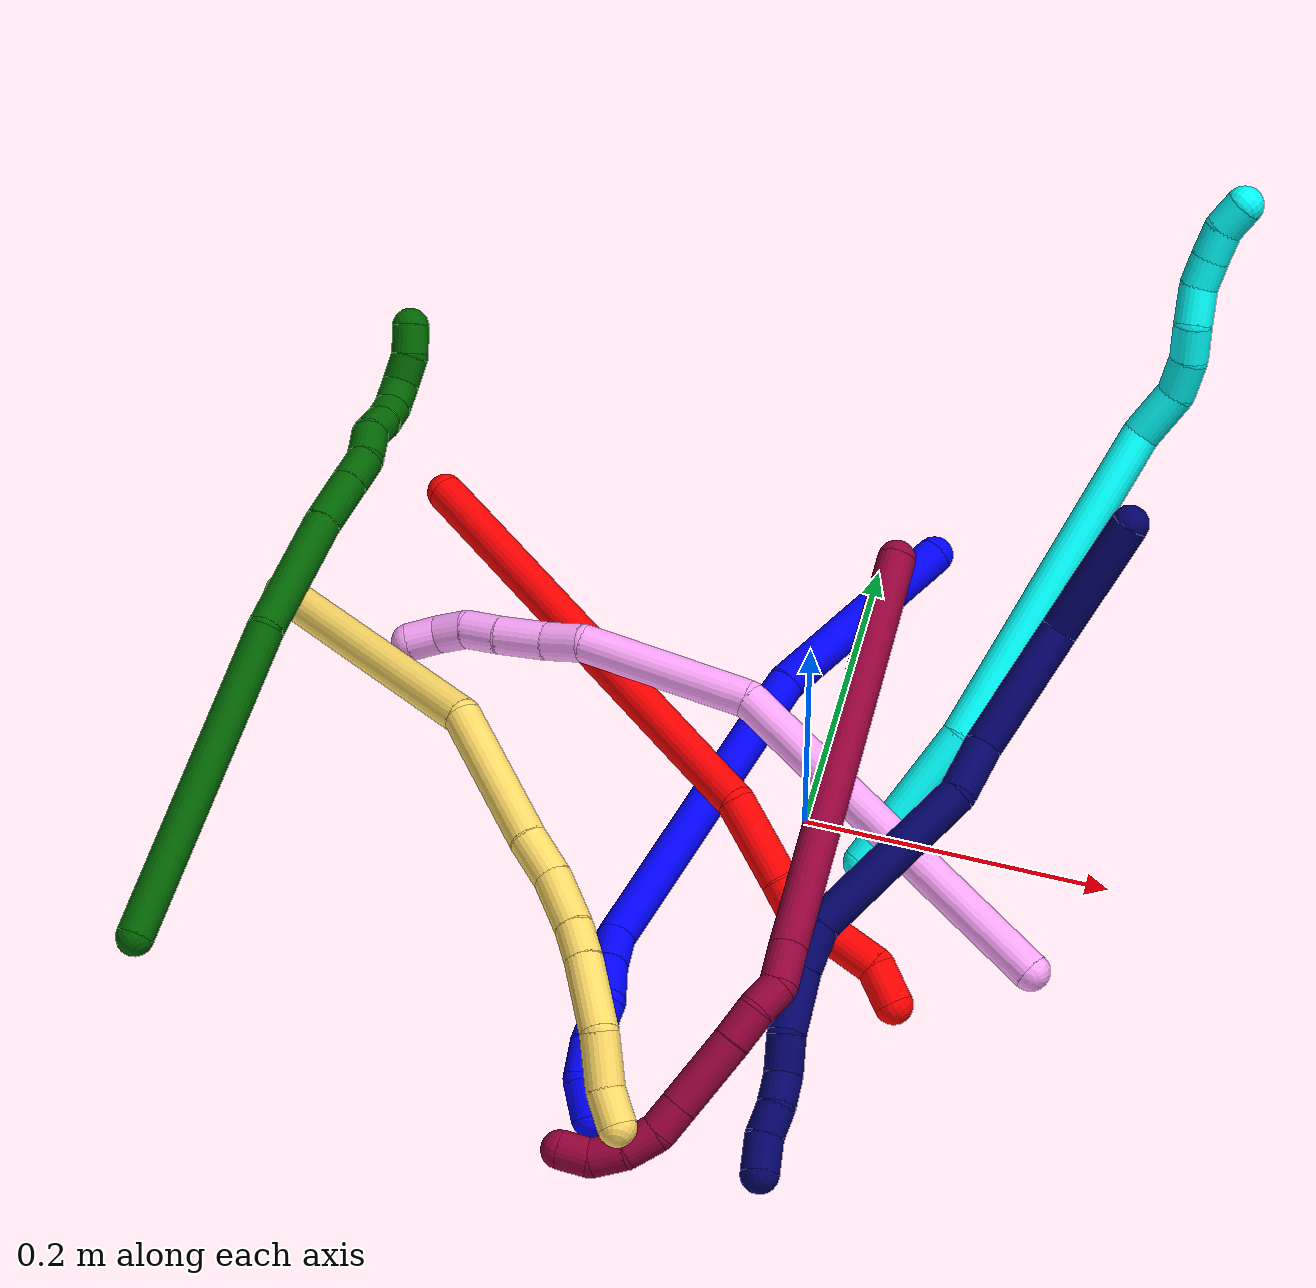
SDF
<sdf version="1.7">
 <world name="default">
  <plugin name="TubeGeneratorPlugin" filename="libtube_generator_plugin.so"/>
  <model name="photoneo_s_sensor">
   <static>1</static>
   <pose>0 0 2 1.57079 1.57079 3.14159</pose>
   <link name="link">
    <inertial><mass>0.1</mass></inertial>
    <sensor name="sensor" type="depth">
     <update_rate>30</update_rate>
     <camera>
      <horizontal_fov>1.22</horizontal_fov>
      <image><width>1920</width><height>1200</height><format>B8G8R8</format></image>
      <clip><near>0.1</near><far>4</far></clip>
      <depth_camera><output>points</output></depth_camera>
     </camera>
     <plugin name="camera_plugin" filename="libgazebo_ros_depth_camera.so">
      <baseline>0.2</baseline>
      <alwaysOn>1</alwaysOn>
      <updateRate>0.0</updateRate>
      <cameraName>camera_ir</cameraName>
      <imageTopicName>/camera/color/image_raw</imageTopicName>
      <cameraInfoTopicName>/camera/color/camera_info</cameraInfoTopicName>
      <depthImageTopicName>/camera/depth/image_raw</depthImageTopicName>
      <depthImageCameraInfoTopicName>/camera/depth/camera_info</depthImageCameraInfoTopicName>
      <pointCloudTopicName>/camera/depth/points</pointCloudTopicName>
      <frameName>fr_optical</frameName>
      <pointCloudCutoff>0.1</pointCloudCutoff>
      <pointCloudCutoffMax>2.0</pointCloudCutoffMax>
      <distortionK1>0</distortionK1>
      <distortionK2>0</distortionK2>
      <distortionK3>0</distortionK3>
      <distortionT1>0</distortionT1>
      <distortionT2>0</distortionT2>
      <CxPrime>0</CxPrime>
      <Cx>0</Cx>
      <Cy>0</Cy>
      <focalLength>0</focalLength>
      <hackBaseline>0</hackBaseline>
     </plugin>
    </sensor>
   </link>
  </model>
  <gravity>0 0 -9.8</gravity>
  <magnetic_field>6e-06 2.3e-05 -4.2e-05</magnetic_field>
  <atmosphere type="adiabatic"/>
  <physics name="default_physics" default="0" type="ode">
   <max_step_size>0.003</max_step_size>
   <real_time_factor>1</real_time_factor>
   <real_time_update_rate>1000</real_time_update_rate>
   <max_contacts>10000</max_contacts>
   <ode>
    <solver>
     <type>quick</type>
     <iters>100</iters>
     <sor>1.3</sor>
     <use_dynamic_moi_rescaling>0</use_dynamic_moi_rescaling>
    </solver>
    <constraints>
     <contact_max_correcting_vel>0</contact_max_correcting_vel>
     <contact_surface_layer>0.001</contact_surface_layer>
     <cfm>0</cfm>
     <erp>0.2</erp>
    </constraints>
   </ode>
  </physics>
  <scene><ambient>0.4 0.4 0.4 1</ambient><background>0.7 0.7 0.7 1</background><shadows>0</shadows></scene>
  <audio><device>default</device></audio>
  <spherical_coordinates>
   <surface_model>EARTH_WGS84</surface_model>
   <latitude_deg>0</latitude_deg>
   <longitude_deg>0</longitude_deg>
   <elevation>0</elevation>
   <heading_deg>0</heading_deg>
  </spherical_coordinates>
  <model name="bin">
   <static>1</static>
   <link name="bottom">
    <collision name="collision-bottom">
     <pose>0 0 -0.01 0 -0 0</pose>
     <geometry><box><size>0.8 0.6 0.02</size></box></geometry>
     <surface>
      <friction><ode><mu>100</mu><mu2>100</mu2></ode></friction>
      <contact><collide_bitmask>65535</collide_bitmask></contact>
     </surface>
    </collision>
   </link>
   <link name="west_wall">
    <collision name="collision-west_wall">
     <pose>-0.41 0 0.1 0 -0 0</pose>
     <geometry><box><size>0.02 0.6 0.2</size></box></geometry>
     <surface>
      <friction><ode><mu>100</mu><mu2>100</mu2></ode></friction>
      <contact><collide_bitmask>65535</collide_bitmask></contact>
     </surface>
    </collision>
   </link>
   <link name="east_wall">
    <collision name="collision-east_wall">
     <pose>0.41 0 0.1 0 -0 0</pose>
     <geometry><box><size>0.02 0.6 0.2</size></box></geometry>
     <surface>
      <friction><ode><mu>100</mu><mu2>100</mu2></ode></friction>
      <contact><collide_bitmask>65535</collide_bitmask></contact>
     </surface>
    </collision>
   </link>
   <link name="south_wall">
    <collision name="collision-south_wall">
     <pose>0 -0.31 0.1 0 -0 0</pose>
     <geometry><box><size>0.8 0.02 0.2</size></box></geometry>
     <surface>
      <friction><ode><mu>100</mu><mu2>100</mu2></ode></friction>
      <contact><collide_bitmask>65535</collide_bitmask></contact>
     </surface>
    </collision>
   </link>
   <link name="north_wall">
    <collision name="collision-north_wall">
     <pose>0 0.31 0.1 0 -0 0</pose>
     <geometry><box><size>0.8 0.02 0.2</size></box></geometry>
     <surface>
      <friction><ode><mu>100</mu><mu2>100</mu2></ode></friction>
      <contact><collide_bitmask>65535</collide_bitmask></contact>
     </surface>
    </collision>
   </link>
  </model>
  <model name="1">
   <static>0</static>
   <link name="1">
    <collision name="collision-cylinder-e_1_1_4">
     <pose>-0.031318 -0.049435 0.041776 0.869175 -0.450663 -0.212007</pose>
     <geometry><cylinder><radius>0.0125</radius><length>0.143803</length></cylinder></geometry>
     <surface>
      <friction><ode><mu>1.16</mu><mu2>1.16</mu2><slip1>0</slip1><slip2>0</slip2></ode></friction>
      <contact><ode><kp>1e+06</kp><kd>1</kd><max_vel>0</max_vel><min_depth>0.001</min_depth></ode></contact>
     </surface>
    </collision>
    <visual name="visual-cylinder-e_1_1_4">
     <pose>-0.031318 -0.049435 0.041776 0.869175 -0.450663 -0.212007</pose>
     <geometry><cylinder><radius>0.0125</radius><length>0.143803</length></cylinder></geometry>
     <material><ambient>0 0 1 1</ambient></material>
    </visual>
    <collision name="collision-cylinder-e_2_4_5">
     <pose>-0.109671 -0.188488 0.124646 1.14085 -0.445147 -0.288389</pose>
     <geometry><cylinder><radius>0.0125</radius><length>0.218472</length></cylinder></geometry>
     <surface>
      <friction><ode><mu>1.16</mu><mu2>1.16</mu2><slip1>0</slip1><slip2>0</slip2></ode></friction>
      <contact><ode><kp>1e+06</kp><kd>1</kd><max_vel>0</max_vel><min_depth>0.001</min_depth></ode></contact>
     </surface>
    </collision>
    <visual name="visual-cylinder-e_2_4_5">
     <pose>-0.109671 -0.188488 0.124646 1.14085 -0.445147 -0.288389</pose>
     <geometry><cylinder><radius>0.0125</radius><length>0.218472</length></cylinder></geometry>
     <material><ambient>0 0 1 1</ambient></material>
    </visual>
    <collision name="collision-cylinder-e_3_5_6">
     <pose>-0.157095 -0.29198 0.168436 1.37884 -0.027443 -0.022623</pose>
     <geometry><cylinder><radius>0.0125</radius><length>0.028279</length></cylinder></geometry>
     <surface>
      <friction><ode><mu>1.16</mu><mu2>1.16</mu2><slip1>0</slip1><slip2>0</slip2></ode></friction>
      <contact><ode><kp>1e+06</kp><kd>1</kd><max_vel>0</max_vel><min_depth>0.001</min_depth></ode></contact>
     </surface>
    </collision>
    <visual name="visual-cylinder-e_3_5_6">
     <pose>-0.157095 -0.29198 0.168436 1.37884 -0.027443 -0.022623</pose>
     <geometry><cylinder><radius>0.0125</radius><length>0.028279</length></cylinder></geometry>
     <material><ambient>0 0 1 1</ambient></material>
    </visual>
    <collision name="collision-cylinder-e_4_6_7">
     <pose>-0.157898 -0.321105 0.171953 1.5171 -0.027157 -0.025737</pose>
     <geometry><cylinder><radius>0.0125</radius><length>0.030557</length></cylinder></geometry>
     <surface>
      <friction><ode><mu>1.16</mu><mu2>1.16</mu2><slip1>0</slip1><slip2>0</slip2></ode></friction>
      <contact><ode><kp>1e+06</kp><kd>1</kd><max_vel>0</max_vel><min_depth>0.001</min_depth></ode></contact>
     </surface>
    </collision>
    <visual name="visual-cylinder-e_4_6_7">
     <pose>-0.157898 -0.321105 0.171953 1.5171 -0.027157 -0.025737</pose>
     <geometry><cylinder><radius>0.0125</radius><length>0.030557</length></cylinder></geometry>
     <material><ambient>0 0 1 1</ambient></material>
    </visual>
    <collision name="collision-cylinder-e_5_7_8">
     <pose>-0.165688 -0.348756 0.175247 1.3738 -0.528014 -0.436334</pose>
     <geometry><cylinder><radius>0.0125</radius><length>0.029277</length></cylinder></geometry>
     <surface>
      <friction><ode><mu>1.16</mu><mu2>1.16</mu2><slip1>0</slip1><slip2>0</slip2></ode></friction>
      <contact><ode><kp>1e+06</kp><kd>1</kd><max_vel>0</max_vel><min_depth>0.001</min_depth></ode></contact>
     </surface>
    </collision>
    <visual name="visual-cylinder-e_5_7_8">
     <pose>-0.165688 -0.348756 0.175247 1.3738 -0.528014 -0.436334</pose>
     <geometry><cylinder><radius>0.0125</radius><length>0.029277</length></cylinder></geometry>
     <material><ambient>0 0 1 1</ambient></material>
    </visual>
    <collision name="collision-cylinder-e_6_8_9">
     <pose>-0.177675 -0.372837 0.178239 1.52658 -0.37575 -0.35985</pose>
     <geometry><cylinder><radius>0.0125</radius><length>0.025137</length></cylinder></geometry>
     <surface>
      <friction><ode><mu>1.16</mu><mu2>1.16</mu2><slip1>0</slip1><slip2>0</slip2></ode></friction>
      <contact><ode><kp>1e+06</kp><kd>1</kd><max_vel>0</max_vel><min_depth>0.001</min_depth></ode></contact>
     </surface>
    </collision>
    <visual name="visual-cylinder-e_6_8_9">
     <pose>-0.177675 -0.372837 0.178239 1.52658 -0.37575 -0.35985</pose>
     <geometry><cylinder><radius>0.0125</radius><length>0.025137</length></cylinder></geometry>
     <material><ambient>0 0 1 1</ambient></material>
    </visual>
    <collision name="collision-cylinder-e_7_9_2">
     <pose>-0.187763 -0.394217 0.173686 2.05242 -0.463854 -0.743599</pose>
     <geometry><cylinder><radius>0.0125</radius><length>0.024476</length></cylinder></geometry>
     <surface>
      <friction><ode><mu>1.16</mu><mu2>1.16</mu2><slip1>0</slip1><slip2>0</slip2></ode></friction>
      <contact><ode><kp>1e+06</kp><kd>1</kd><max_vel>0</max_vel><min_depth>0.001</min_depth></ode></contact>
     </surface>
    </collision>
    <visual name="visual-cylinder-e_7_9_2">
     <pose>-0.187763 -0.394217 0.173686 2.05242 -0.463854 -0.743599</pose>
     <geometry><cylinder><radius>0.0125</radius><length>0.024476</length></cylinder></geometry>
     <material><ambient>0 0 1 1</ambient></material>
    </visual>
    <collision name="collision-sphere-2">
     <pose>-0.193238 -0.403917 0.168616 0 -0 0</pose>
     <geometry><sphere><radius>0.0125</radius></sphere></geometry>
     <surface>
      <friction><ode><mu>1.16</mu><mu2>1.16</mu2><slip1>0</slip1><slip2>0</slip2></ode></friction>
      <contact><ode><kp>1e+06</kp><kd>1</kd><max_vel>0</max_vel><min_depth>0.001</min_depth></ode></contact>
     </surface>
    </collision>
    <visual name="visual-sphere-2">
     <pose>-0.193238 -0.403917 0.168616 0 -0 0</pose>
     <geometry><sphere><radius>0.0125</radius></sphere></geometry>
     <material><ambient>0 0 1 1</ambient></material>
    </visual>
    <collision name="collision-sphere-9">
     <pose>-0.182287 -0.384517 0.178756 0 -0 0</pose>
     <geometry><sphere><radius>0.0125</radius></sphere></geometry>
     <surface>
      <friction><ode><mu>1.16</mu><mu2>1.16</mu2><slip1>0</slip1><slip2>0</slip2></ode></friction>
      <contact><ode><kp>1e+06</kp><kd>1</kd><max_vel>0</max_vel><min_depth>0.001</min_depth></ode></contact>
     </surface>
    </collision>
    <visual name="visual-sphere-9">
     <pose>-0.182287 -0.384517 0.178756 0 -0 0</pose>
     <geometry><sphere><radius>0.0125</radius></sphere></geometry>
     <material><ambient>0 0 1 1</ambient></material>
    </visual>
    <collision name="collision-sphere-4">
     <pose>-0.062635 -0.09887 0.083551 0 -0 0</pose>
     <geometry><sphere><radius>0.0125</radius></sphere></geometry>
     <surface>
      <friction><ode><mu>1.16</mu><mu2>1.16</mu2><slip1>0</slip1><slip2>0</slip2></ode></friction>
      <contact><ode><kp>1e+06</kp><kd>1</kd><max_vel>0</max_vel><min_depth>0.001</min_depth></ode></contact>
     </surface>
    </collision>
    <visual name="visual-sphere-4">
     <pose>-0.062635 -0.09887 0.083551 0 -0 0</pose>
     <geometry><sphere><radius>0.0125</radius></sphere></geometry>
     <material><ambient>0 0 1 1</ambient></material>
    </visual>
    <collision name="collision-sphere-1">
     <geometry><sphere><radius>0.0125</radius></sphere></geometry>
     <surface>
      <friction><ode><mu>1.16</mu><mu2>1.16</mu2><slip1>0</slip1><slip2>0</slip2></ode></friction>
      <contact><ode><kp>1e+06</kp><kd>1</kd><max_vel>0</max_vel><min_depth>0.001</min_depth></ode></contact>
     </surface>
    </collision>
    <visual name="visual-sphere-1">
     <geometry><sphere><radius>0.0125</radius></sphere></geometry>
     <material><ambient>0 0 1 1</ambient></material>
    </visual>
    <collision name="collision-sphere-8">
     <pose>-0.173063 -0.361157 0.177722 0 -0 0</pose>
     <geometry><sphere><radius>0.0125</radius></sphere></geometry>
     <surface>
      <friction><ode><mu>1.16</mu><mu2>1.16</mu2><slip1>0</slip1><slip2>0</slip2></ode></friction>
      <contact><ode><kp>1e+06</kp><kd>1</kd><max_vel>0</max_vel><min_depth>0.001</min_depth></ode></contact>
     </surface>
    </collision>
    <visual name="visual-sphere-8">
     <pose>-0.173063 -0.361157 0.177722 0 -0 0</pose>
     <geometry><sphere><radius>0.0125</radius></sphere></geometry>
     <material><ambient>0 0 1 1</ambient></material>
    </visual>
    <collision name="collision-sphere-5">
     <pose>-0.156707 -0.278105 0.16574 0 -0 0</pose>
     <geometry><sphere><radius>0.0125</radius></sphere></geometry>
     <surface>
      <friction><ode><mu>1.16</mu><mu2>1.16</mu2><slip1>0</slip1><slip2>0</slip2></ode></friction>
      <contact><ode><kp>1e+06</kp><kd>1</kd><max_vel>0</max_vel><min_depth>0.001</min_depth></ode></contact>
     </surface>
    </collision>
    <visual name="visual-sphere-5">
     <pose>-0.156707 -0.278105 0.16574 0 -0 0</pose>
     <geometry><sphere><radius>0.0125</radius></sphere></geometry>
     <material><ambient>0 0 1 1</ambient></material>
    </visual>
    <collision name="collision-sphere-6">
     <pose>-0.157483 -0.305854 0.171133 0 -0 0</pose>
     <geometry><sphere><radius>0.0125</radius></sphere></geometry>
     <surface>
      <friction><ode><mu>1.16</mu><mu2>1.16</mu2><slip1>0</slip1><slip2>0</slip2></ode></friction>
      <contact><ode><kp>1e+06</kp><kd>1</kd><max_vel>0</max_vel><min_depth>0.001</min_depth></ode></contact>
     </surface>
    </collision>
    <visual name="visual-sphere-6">
     <pose>-0.157483 -0.305854 0.171133 0 -0 0</pose>
     <geometry><sphere><radius>0.0125</radius></sphere></geometry>
     <material><ambient>0 0 1 1</ambient></material>
    </visual>
    <collision name="collision-sphere-7">
     <pose>-0.158312 -0.336356 0.172773 0 -0 0</pose>
     <geometry><sphere><radius>0.0125</radius></sphere></geometry>
     <surface>
      <friction><ode><mu>1.16</mu><mu2>1.16</mu2><slip1>0</slip1><slip2>0</slip2></ode></friction>
      <contact><ode><kp>1e+06</kp><kd>1</kd><max_vel>0</max_vel><min_depth>0.001</min_depth></ode></contact>
     </surface>
    </collision>
    <visual name="visual-sphere-7">
     <pose>-0.158312 -0.336356 0.172773 0 -0 0</pose>
     <geometry><sphere><radius>0.0125</radius></sphere></geometry>
     <material><ambient>0 0 1 1</ambient></material>
    </visual>
    <inertial>
     <pose>-0.103287 -0.191177 0.114238 0 -0 0</pose>
     <mass>0.5</mass>
     <inertia>
      <ixx>0.000703</ixx>
      <ixy>0</ixy>
      <ixz>0</ixz>
      <iyy>0.00032</iyy>
      <iyz>0</iyz>
      <izz>0.001412</izz>
     </inertia>
    </inertial>
   </link>
   <pose>0.03379 0.215487 0.0123 -0.536003 -1.06983 0.766493</pose>
  </model>
  <model name="2">
   <static>0</static>
   <link name="2">
    <collision name="collision-cylinder-e_1_1_4">
     <pose>0.081137 -0.069996 -0.12552 2.6329 0.51395 1.58154</pose>
     <geometry><cylinder><radius>0.0125</radius><length>0.330078</length></cylinder></geometry>
     <surface>
      <friction><ode><mu>1.16</mu><mu2>1.16</mu2><slip1>0</slip1><slip2>0</slip2></ode></friction>
      <contact><ode><kp>1e+06</kp><kd>1</kd><max_vel>0</max_vel><min_depth>0.001</min_depth></ode></contact>
     </surface>
    </collision>
    <visual name="visual-cylinder-e_1_1_4">
     <pose>0.081137 -0.069996 -0.12552 2.6329 0.51395 1.58154</pose>
     <geometry><cylinder><radius>0.0125</radius><length>0.330078</length></cylinder></geometry>
     <material><ambient>1 0 0 1</ambient></material>
    </visual>
    <collision name="collision-cylinder-e_2_4_5">
     <pose>0.166741 -0.150161 -0.278185 2.78316 0.152918 0.800146</pose>
     <geometry><cylinder><radius>0.0125</radius><length>0.058659</length></cylinder></geometry>
     <surface>
      <friction><ode><mu>1.16</mu><mu2>1.16</mu2><slip1>0</slip1><slip2>0</slip2></ode></friction>
      <contact><ode><kp>1e+06</kp><kd>1</kd><max_vel>0</max_vel><min_depth>0.001</min_depth></ode></contact>
     </surface>
    </collision>
    <visual name="visual-cylinder-e_2_4_5">
     <pose>0.166741 -0.150161 -0.278185 2.78316 0.152918 0.800146</pose>
     <geometry><cylinder><radius>0.0125</radius><length>0.058659</length></cylinder></geometry>
     <material><ambient>1 0 0 1</ambient></material>
    </visual>
    <collision name="collision-cylinder-e_3_5_6">
     <pose>0.171756 -0.162935 -0.315049 2.87965 0.054406 0.407399</pose>
     <geometry><cylinder><radius>0.0125</radius><length>0.020155</length></cylinder></geometry>
     <surface>
      <friction><ode><mu>1.16</mu><mu2>1.16</mu2><slip1>0</slip1><slip2>0</slip2></ode></friction>
      <contact><ode><kp>1e+06</kp><kd>1</kd><max_vel>0</max_vel><min_depth>0.001</min_depth></ode></contact>
     </surface>
    </collision>
    <visual name="visual-cylinder-e_3_5_6">
     <pose>0.171756 -0.162935 -0.315049 2.87965 0.054406 0.407399</pose>
     <geometry><cylinder><radius>0.0125</radius><length>0.020155</length></cylinder></geometry>
     <material><ambient>1 0 0 1</ambient></material>
    </visual>
    <collision name="collision-cylinder-e_4_6_7">
     <pose>0.188183 -0.16862 -0.352307 3.03024 0.520354 2.72884</pose>
     <geometry><cylinder><radius>0.0125</radius><length>0.063874</length></cylinder></geometry>
     <surface>
      <friction><ode><mu>1.16</mu><mu2>1.16</mu2><slip1>0</slip1><slip2>0</slip2></ode></friction>
      <contact><ode><kp>1e+06</kp><kd>1</kd><max_vel>0</max_vel><min_depth>0.001</min_depth></ode></contact>
     </surface>
    </collision>
    <visual name="visual-cylinder-e_4_6_7">
     <pose>0.188183 -0.16862 -0.352307 3.03024 0.520354 2.72884</pose>
     <geometry><cylinder><radius>0.0125</radius><length>0.063874</length></cylinder></geometry>
     <material><ambient>1 0 0 1</ambient></material>
    </visual>
    <collision name="collision-cylinder-e_5_7_2">
     <pose>0.205117 -0.176683 -0.392474 2.76574 0.077582 0.402636</pose>
     <geometry><cylinder><radius>0.0125</radius><length>0.027235</length></cylinder></geometry>
     <surface>
      <friction><ode><mu>1.16</mu><mu2>1.16</mu2><slip1>0</slip1><slip2>0</slip2></ode></friction>
      <contact><ode><kp>1e+06</kp><kd>1</kd><max_vel>0</max_vel><min_depth>0.001</min_depth></ode></contact>
     </surface>
    </collision>
    <visual name="visual-cylinder-e_5_7_2">
     <pose>0.205117 -0.176683 -0.392474 2.76574 0.077582 0.402636</pose>
     <geometry><cylinder><radius>0.0125</radius><length>0.027235</length></cylinder></geometry>
     <material><ambient>1 0 0 1</ambient></material>
    </visual>
    <collision name="collision-sphere-2">
     <pose>0.206172 -0.181666 -0.405102 0 -0 0</pose>
     <geometry><sphere><radius>0.0125</radius></sphere></geometry>
     <surface>
      <friction><ode><mu>1.16</mu><mu2>1.16</mu2><slip1>0</slip1><slip2>0</slip2></ode></friction>
      <contact><ode><kp>1e+06</kp><kd>1</kd><max_vel>0</max_vel><min_depth>0.001</min_depth></ode></contact>
     </surface>
    </collision>
    <visual name="visual-sphere-2">
     <pose>0.206172 -0.181666 -0.405102 0 -0 0</pose>
     <geometry><sphere><radius>0.0125</radius></sphere></geometry>
     <material><ambient>1 0 0 1</ambient></material>
    </visual>
    <collision name="collision-sphere-7">
     <pose>0.204062 -0.171699 -0.379845 0 -0 0</pose>
     <geometry><sphere><radius>0.0125</radius></sphere></geometry>
     <surface>
      <friction><ode><mu>1.16</mu><mu2>1.16</mu2><slip1>0</slip1><slip2>0</slip2></ode></friction>
      <contact><ode><kp>1e+06</kp><kd>1</kd><max_vel>0</max_vel><min_depth>0.001</min_depth></ode></contact>
     </surface>
    </collision>
    <visual name="visual-sphere-7">
     <pose>0.204062 -0.171699 -0.379845 0 -0 0</pose>
     <geometry><sphere><radius>0.0125</radius></sphere></geometry>
     <material><ambient>1 0 0 1</ambient></material>
    </visual>
    <collision name="collision-sphere-6">
     <pose>0.172304 -0.165541 -0.324769 0 -0 0</pose>
     <geometry><sphere><radius>0.0125</radius></sphere></geometry>
     <surface>
      <friction><ode><mu>1.16</mu><mu2>1.16</mu2><slip1>0</slip1><slip2>0</slip2></ode></friction>
      <contact><ode><kp>1e+06</kp><kd>1</kd><max_vel>0</max_vel><min_depth>0.001</min_depth></ode></contact>
     </surface>
    </collision>
    <visual name="visual-sphere-6">
     <pose>0.172304 -0.165541 -0.324769 0 -0 0</pose>
     <geometry><sphere><radius>0.0125</radius></sphere></geometry>
     <material><ambient>1 0 0 1</ambient></material>
    </visual>
    <collision name="collision-sphere-5">
     <pose>0.171208 -0.160329 -0.30533 0 -0 0</pose>
     <geometry><sphere><radius>0.0125</radius></sphere></geometry>
     <surface>
      <friction><ode><mu>1.16</mu><mu2>1.16</mu2><slip1>0</slip1><slip2>0</slip2></ode></friction>
      <contact><ode><kp>1e+06</kp><kd>1</kd><max_vel>0</max_vel><min_depth>0.001</min_depth></ode></contact>
     </surface>
    </collision>
    <visual name="visual-sphere-5">
     <pose>0.171208 -0.160329 -0.30533 0 -0 0</pose>
     <geometry><sphere><radius>0.0125</radius></sphere></geometry>
     <material><ambient>1 0 0 1</ambient></material>
    </visual>
    <collision name="collision-sphere-1">
     <geometry><sphere><radius>0.0125</radius></sphere></geometry>
     <surface>
      <friction><ode><mu>1.16</mu><mu2>1.16</mu2><slip1>0</slip1><slip2>0</slip2></ode></friction>
      <contact><ode><kp>1e+06</kp><kd>1</kd><max_vel>0</max_vel><min_depth>0.001</min_depth></ode></contact>
     </surface>
    </collision>
    <visual name="visual-sphere-1">
     <geometry><sphere><radius>0.0125</radius></sphere></geometry>
     <material><ambient>1 0 0 1</ambient></material>
    </visual>
    <collision name="collision-sphere-4">
     <pose>0.162273 -0.139992 -0.25104 0 -0 0</pose>
     <geometry><sphere><radius>0.0125</radius></sphere></geometry>
     <surface>
      <friction><ode><mu>1.16</mu><mu2>1.16</mu2><slip1>0</slip1><slip2>0</slip2></ode></friction>
      <contact><ode><kp>1e+06</kp><kd>1</kd><max_vel>0</max_vel><min_depth>0.001</min_depth></ode></contact>
     </surface>
    </collision>
    <visual name="visual-sphere-4">
     <pose>0.162273 -0.139992 -0.25104 0 -0 0</pose>
     <geometry><sphere><radius>0.0125</radius></sphere></geometry>
     <material><ambient>1 0 0 1</ambient></material>
    </visual>
    <inertial>
     <pose>0.11526 -0.101557 -0.194582 0 -0 0</pose>
     <mass>0.5</mass>
     <inertia>
      <ixx>0.00263</ixx>
      <ixy>0</ixy>
      <ixz>0</ixz>
      <iyy>0.003386</iyy>
      <iyz>0</iyz>
      <izz>-0.00024</izz>
     </inertia>
    </inertial>
   </link>
   <pose>-0.293218 0.182097 0.011497 -0.648879 -0.801663 0.244757</pose>
  </model>
  <model name="3">
   <static>0</static>
   <link name="3">
    <collision name="collision-cylinder-e_1_1_4">
     <pose>-0.017262 0.018771 0.044118 -0.402267 -0.345593 0.071143</pose>
     <geometry><cylinder><radius>0.0125</radius><length>0.101917</length></cylinder></geometry>
     <surface>
      <friction><ode><mu>1.16</mu><mu2>1.16</mu2><slip1>0</slip1><slip2>0</slip2></ode></friction>
      <contact><ode><kp>1e+06</kp><kd>1</kd><max_vel>0</max_vel><min_depth>0.001</min_depth></ode></contact>
     </surface>
    </collision>
    <visual name="visual-cylinder-e_1_1_4">
     <pose>-0.017262 0.018771 0.044118 -0.402267 -0.345593 0.071143</pose>
     <geometry><cylinder><radius>0.0125</radius><length>0.101917</length></cylinder></geometry>
     <material><ambient>0.003922 1 0.996078 1</ambient></material>
    </visual>
    <collision name="collision-cylinder-e_2_4_5">
     <pose>-0.049064 0.080925 0.192293 -0.395008 -0.128255 0.025699</pose>
     <geometry><cylinder><radius>0.0125</radius><length>0.227343</length></cylinder></geometry>
     <surface>
      <friction><ode><mu>1.16</mu><mu2>1.16</mu2><slip1>0</slip1><slip2>0</slip2></ode></friction>
      <contact><ode><kp>1e+06</kp><kd>1</kd><max_vel>0</max_vel><min_depth>0.001</min_depth></ode></contact>
     </surface>
    </collision>
    <visual name="visual-cylinder-e_2_4_5">
     <pose>-0.049064 0.080925 0.192293 -0.395008 -0.128255 0.025699</pose>
     <geometry><cylinder><radius>0.0125</radius><length>0.227343</length></cylinder></geometry>
     <material><ambient>0.003922 1 0.996078 1</ambient></material>
    </visual>
    <collision name="collision-cylinder-e_3_5_6">
     <pose>-0.073799 0.132122 0.309065 -0.551021 -0.599329 0.174248</pose>
     <geometry><cylinder><radius>0.0125</radius><length>0.03615</length></cylinder></geometry>
     <surface>
      <friction><ode><mu>1.16</mu><mu2>1.16</mu2><slip1>0</slip1><slip2>0</slip2></ode></friction>
      <contact><ode><kp>1e+06</kp><kd>1</kd><max_vel>0</max_vel><min_depth>0.001</min_depth></ode></contact>
     </surface>
    </collision>
    <visual name="visual-cylinder-e_3_5_6">
     <pose>-0.073799 0.132122 0.309065 -0.551021 -0.599329 0.174248</pose>
     <geometry><cylinder><radius>0.0125</radius><length>0.03615</length></cylinder></geometry>
     <material><ambient>0.003922 1 0.996078 1</ambient></material>
    </visual>
    <collision name="collision-cylinder-e_4_6_7">
     <pose>-0.090062 0.149251 0.328163 -0.970026 -0.493037 0.263686</pose>
     <geometry><cylinder><radius>0.0125</radius><length>0.025637</length></cylinder></geometry>
     <surface>
      <friction><ode><mu>1.16</mu><mu2>1.16</mu2><slip1>0</slip1><slip2>0</slip2></ode></friction>
      <contact><ode><kp>1e+06</kp><kd>1</kd><max_vel>0</max_vel><min_depth>0.001</min_depth></ode></contact>
     </surface>
    </collision>
    <visual name="visual-cylinder-e_4_6_7">
     <pose>-0.090062 0.149251 0.328163 -0.970026 -0.493037 0.263686</pose>
     <geometry><cylinder><radius>0.0125</radius><length>0.025637</length></cylinder></geometry>
     <material><ambient>0.003922 1 0.996078 1</ambient></material>
    </visual>
    <collision name="collision-cylinder-e_5_7_8">
     <pose>-0.099192 0.168243 0.339845 -1.06988 -0.270779 0.161095</pose>
     <geometry><cylinder><radius>0.0125</radius><length>0.022902</length></cylinder></geometry>
     <surface>
      <friction><ode><mu>1.16</mu><mu2>1.16</mu2><slip1>0</slip1><slip2>0</slip2></ode></friction>
      <contact><ode><kp>1e+06</kp><kd>1</kd><max_vel>0</max_vel><min_depth>0.001</min_depth></ode></contact>
     </surface>
    </collision>
    <visual name="visual-cylinder-e_5_7_8">
     <pose>-0.099192 0.168243 0.339845 -1.06988 -0.270779 0.161095</pose>
     <geometry><cylinder><radius>0.0125</radius><length>0.022902</length></cylinder></geometry>
     <material><ambient>0.003922 1 0.996078 1</ambient></material>
    </visual>
    <collision name="collision-cylinder-e_6_8_9">
     <pose>-0.102839 0.187006 0.353484 -0.828069 -0.047341 0.020806</pose>
     <geometry><cylinder><radius>0.0125</radius><length>0.024693</length></cylinder></geometry>
     <surface>
      <friction><ode><mu>1.16</mu><mu2>1.16</mu2><slip1>0</slip1><slip2>0</slip2></ode></friction>
      <contact><ode><kp>1e+06</kp><kd>1</kd><max_vel>0</max_vel><min_depth>0.001</min_depth></ode></contact>
     </surface>
    </collision>
    <visual name="visual-cylinder-e_6_8_9">
     <pose>-0.102839 0.187006 0.353484 -0.828069 -0.047341 0.020806</pose>
     <geometry><cylinder><radius>0.0125</radius><length>0.024693</length></cylinder></geometry>
     <material><ambient>0.003922 1 0.996078 1</ambient></material>
    </visual>
    <collision name="collision-cylinder-e_7_9_10">
     <pose>-0.106938 0.202754 0.368474 -0.786499 -0.357366 0.149575</pose>
     <geometry><cylinder><radius>0.0125</radius><length>0.020097</length></cylinder></geometry>
     <surface>
      <friction><ode><mu>1.16</mu><mu2>1.16</mu2><slip1>0</slip1><slip2>0</slip2></ode></friction>
      <contact><ode><kp>1e+06</kp><kd>1</kd><max_vel>0</max_vel><min_depth>0.001</min_depth></ode></contact>
     </surface>
    </collision>
    <visual name="visual-cylinder-e_7_9_10">
     <pose>-0.106938 0.202754 0.368474 -0.786499 -0.357366 0.149575</pose>
     <geometry><cylinder><radius>0.0125</radius><length>0.020097</length></cylinder></geometry>
     <material><ambient>0.003922 1 0.996078 1</ambient></material>
    </visual>
    <collision name="collision-cylinder-e_8_10_11">
     <pose>-0.114739 0.21619 0.381734 -0.797445 -0.425212 0.181387</pose>
     <geometry><cylinder><radius>0.0125</radius><length>0.020778</length></cylinder></geometry>
     <surface>
      <friction><ode><mu>1.16</mu><mu2>1.16</mu2><slip1>0</slip1><slip2>0</slip2></ode></friction>
      <contact><ode><kp>1e+06</kp><kd>1</kd><max_vel>0</max_vel><min_depth>0.001</min_depth></ode></contact>
     </surface>
    </collision>
    <visual name="visual-cylinder-e_8_10_11">
     <pose>-0.114739 0.21619 0.381734 -0.797445 -0.425212 0.181387</pose>
     <geometry><cylinder><radius>0.0125</radius><length>0.020778</length></cylinder></geometry>
     <material><ambient>0.003922 1 0.996078 1</ambient></material>
    </visual>
    <collision name="collision-cylinder-e_9_11_2">
     <pose>-0.125199 0.227208 0.395327 -0.546297 -0.647039 0.187319</pose>
     <geometry><cylinder><radius>0.0125</radius><length>0.020484</length></cylinder></geometry>
     <surface>
      <friction><ode><mu>1.16</mu><mu2>1.16</mu2><slip1>0</slip1><slip2>0</slip2></ode></friction>
      <contact><ode><kp>1e+06</kp><kd>1</kd><max_vel>0</max_vel><min_depth>0.001</min_depth></ode></contact>
     </surface>
    </collision>
    <visual name="visual-cylinder-e_9_11_2">
     <pose>-0.125199 0.227208 0.395327 -0.546297 -0.647039 0.187319</pose>
     <geometry><cylinder><radius>0.0125</radius><length>0.020484</length></cylinder></geometry>
     <material><ambient>0.003922 1 0.996078 1</ambient></material>
    </visual>
    <collision name="collision-sphere-2">
     <pose>-0.131373 0.231453 0.40231 0 -0 0</pose>
     <geometry><sphere><radius>0.0125</radius></sphere></geometry>
     <surface>
      <friction><ode><mu>1.16</mu><mu2>1.16</mu2><slip1>0</slip1><slip2>0</slip2></ode></friction>
      <contact><ode><kp>1e+06</kp><kd>1</kd><max_vel>0</max_vel><min_depth>0.001</min_depth></ode></contact>
     </surface>
    </collision>
    <visual name="visual-sphere-2">
     <pose>-0.131373 0.231453 0.40231 0 -0 0</pose>
     <geometry><sphere><radius>0.0125</radius></sphere></geometry>
     <material><ambient>0.003922 1 0.996078 1</ambient></material>
    </visual>
    <collision name="collision-sphere-11">
     <pose>-0.119024 0.222962 0.388345 0 -0 0</pose>
     <geometry><sphere><radius>0.0125</radius></sphere></geometry>
     <surface>
      <friction><ode><mu>1.16</mu><mu2>1.16</mu2><slip1>0</slip1><slip2>0</slip2></ode></friction>
      <contact><ode><kp>1e+06</kp><kd>1</kd><max_vel>0</max_vel><min_depth>0.001</min_depth></ode></contact>
     </surface>
    </collision>
    <visual name="visual-sphere-11">
     <pose>-0.119024 0.222962 0.388345 0 -0 0</pose>
     <geometry><sphere><radius>0.0125</radius></sphere></geometry>
     <material><ambient>0.003922 1 0.996078 1</ambient></material>
    </visual>
    <collision name="collision-sphere-10">
     <pose>-0.110453 0.209418 0.375123 0 -0 0</pose>
     <geometry><sphere><radius>0.0125</radius></sphere></geometry>
     <surface>
      <friction><ode><mu>1.16</mu><mu2>1.16</mu2><slip1>0</slip1><slip2>0</slip2></ode></friction>
      <contact><ode><kp>1e+06</kp><kd>1</kd><max_vel>0</max_vel><min_depth>0.001</min_depth></ode></contact>
     </surface>
    </collision>
    <visual name="visual-sphere-10">
     <pose>-0.110453 0.209418 0.375123 0 -0 0</pose>
     <geometry><sphere><radius>0.0125</radius></sphere></geometry>
     <material><ambient>0.003922 1 0.996078 1</ambient></material>
    </visual>
    <collision name="collision-sphere-9">
     <pose>-0.103423 0.19609 0.361825 0 -0 0</pose>
     <geometry><sphere><radius>0.0125</radius></sphere></geometry>
     <surface>
      <friction><ode><mu>1.16</mu><mu2>1.16</mu2><slip1>0</slip1><slip2>0</slip2></ode></friction>
      <contact><ode><kp>1e+06</kp><kd>1</kd><max_vel>0</max_vel><min_depth>0.001</min_depth></ode></contact>
     </surface>
    </collision>
    <visual name="visual-sphere-9">
     <pose>-0.103423 0.19609 0.361825 0 -0 0</pose>
     <geometry><sphere><radius>0.0125</radius></sphere></geometry>
     <material><ambient>0.003922 1 0.996078 1</ambient></material>
    </visual>
    <collision name="collision-sphere-4">
     <pose>-0.034525 0.037542 0.088236 0 -0 0</pose>
     <geometry><sphere><radius>0.0125</radius></sphere></geometry>
     <surface>
      <friction><ode><mu>1.16</mu><mu2>1.16</mu2><slip1>0</slip1><slip2>0</slip2></ode></friction>
      <contact><ode><kp>1e+06</kp><kd>1</kd><max_vel>0</max_vel><min_depth>0.001</min_depth></ode></contact>
     </surface>
    </collision>
    <visual name="visual-sphere-4">
     <pose>-0.034525 0.037542 0.088236 0 -0 0</pose>
     <geometry><sphere><radius>0.0125</radius></sphere></geometry>
     <material><ambient>0.003922 1 0.996078 1</ambient></material>
    </visual>
    <collision name="collision-sphere-1">
     <geometry><sphere><radius>0.0125</radius></sphere></geometry>
     <surface>
      <friction><ode><mu>1.16</mu><mu2>1.16</mu2><slip1>0</slip1><slip2>0</slip2></ode></friction>
      <contact><ode><kp>1e+06</kp><kd>1</kd><max_vel>0</max_vel><min_depth>0.001</min_depth></ode></contact>
     </surface>
    </collision>
    <visual name="visual-sphere-1">
     <geometry><sphere><radius>0.0125</radius></sphere></geometry>
     <material><ambient>0.003922 1 0.996078 1</ambient></material>
    </visual>
    <collision name="collision-sphere-8">
     <pose>-0.102255 0.177922 0.345144 0 -0 0</pose>
     <geometry><sphere><radius>0.0125</radius></sphere></geometry>
     <surface>
      <friction><ode><mu>1.16</mu><mu2>1.16</mu2><slip1>0</slip1><slip2>0</slip2></ode></friction>
      <contact><ode><kp>1e+06</kp><kd>1</kd><max_vel>0</max_vel><min_depth>0.001</min_depth></ode></contact>
     </surface>
    </collision>
    <visual name="visual-sphere-8">
     <pose>-0.102255 0.177922 0.345144 0 -0 0</pose>
     <geometry><sphere><radius>0.0125</radius></sphere></geometry>
     <material><ambient>0.003922 1 0.996078 1</ambient></material>
    </visual>
    <collision name="collision-sphere-5">
     <pose>-0.063603 0.124308 0.296349 0 -0 0</pose>
     <geometry><sphere><radius>0.0125</radius></sphere></geometry>
     <surface>
      <friction><ode><mu>1.16</mu><mu2>1.16</mu2><slip1>0</slip1><slip2>0</slip2></ode></friction>
      <contact><ode><kp>1e+06</kp><kd>1</kd><max_vel>0</max_vel><min_depth>0.001</min_depth></ode></contact>
     </surface>
    </collision>
    <visual name="visual-sphere-5">
     <pose>-0.063603 0.124308 0.296349 0 -0 0</pose>
     <geometry><sphere><radius>0.0125</radius></sphere></geometry>
     <material><ambient>0.003922 1 0.996078 1</ambient></material>
    </visual>
    <collision name="collision-sphere-6">
     <pose>-0.083995 0.139936 0.32178 0 -0 0</pose>
     <geometry><sphere><radius>0.0125</radius></sphere></geometry>
     <surface>
      <friction><ode><mu>1.16</mu><mu2>1.16</mu2><slip1>0</slip1><slip2>0</slip2></ode></friction>
      <contact><ode><kp>1e+06</kp><kd>1</kd><max_vel>0</max_vel><min_depth>0.001</min_depth></ode></contact>
     </surface>
    </collision>
    <visual name="visual-sphere-6">
     <pose>-0.083995 0.139936 0.32178 0 -0 0</pose>
     <geometry><sphere><radius>0.0125</radius></sphere></geometry>
     <material><ambient>0.003922 1 0.996078 1</ambient></material>
    </visual>
    <collision name="collision-sphere-7">
     <pose>-0.096129 0.158565 0.334546 0 -0 0</pose>
     <geometry><sphere><radius>0.0125</radius></sphere></geometry>
     <surface>
      <friction><ode><mu>1.16</mu><mu2>1.16</mu2><slip1>0</slip1><slip2>0</slip2></ode></friction>
      <contact><ode><kp>1e+06</kp><kd>1</kd><max_vel>0</max_vel><min_depth>0.001</min_depth></ode></contact>
     </surface>
    </collision>
    <visual name="visual-sphere-7">
     <pose>-0.096129 0.158565 0.334546 0 -0 0</pose>
     <geometry><sphere><radius>0.0125</radius></sphere></geometry>
     <material><ambient>0.003922 1 0.996078 1</ambient></material>
    </visual>
    <inertial>
     <pose>-0.059598 0.10121 0.21549 0 -0 0</pose>
     <mass>0.5</mass>
     <inertia>
      <ixx>0.001104</ixx>
      <ixy>0</ixy>
      <ixz>0</ixz>
      <iyy>0.001063</iyy>
      <iyz>0</iyz>
      <izz>-0.000225</izz>
     </inertia>
    </inertial>
   </link>
   <pose>0.044457 -0.027049 0.011487 1.57606 0.676691 2.66444</pose>
  </model>
  <model name="4">
   <static>0</static>
   <link name="4">
    <collision name="collision-cylinder-e_1_1_4">
     <pose>-0.119549 -0.004277 -0.042734 3.04184 -1.22591 -2.99989</pose>
     <geometry><cylinder><radius>0.0125</radius><length>0.254059</length></cylinder></geometry>
     <surface>
      <friction><ode><mu>1.16</mu><mu2>1.16</mu2><slip1>0</slip1><slip2>0</slip2></ode></friction>
      <contact><ode><kp>1e+06</kp><kd>1</kd><max_vel>0</max_vel><min_depth>0.001</min_depth></ode></contact>
     </surface>
    </collision>
    <visual name="visual-cylinder-e_1_1_4">
     <pose>-0.119549 -0.004277 -0.042734 3.04184 -1.22591 -2.99989</pose>
     <geometry><cylinder><radius>0.0125</radius><length>0.254059</length></cylinder></geometry>
     <material><ambient>1 0.65098 0.996078 1</ambient></material>
    </visual>
    <collision name="collision-cylinder-e_2_4_5">
     <pose>-0.290613 -0.03345 -0.096711 1.995 -1.0832 -1.50024</pose>
     <geometry><cylinder><radius>0.0125</radius><length>0.116619</length></cylinder></geometry>
     <surface>
      <friction><ode><mu>1.16</mu><mu2>1.16</mu2><slip1>0</slip1><slip2>0</slip2></ode></friction>
      <contact><ode><kp>1e+06</kp><kd>1</kd><max_vel>0</max_vel><min_depth>0.001</min_depth></ode></contact>
     </surface>
    </collision>
    <visual name="visual-cylinder-e_2_4_5">
     <pose>-0.290613 -0.03345 -0.096711 1.995 -1.0832 -1.50024</pose>
     <geometry><cylinder><radius>0.0125</radius><length>0.116619</length></cylinder></geometry>
     <material><ambient>1 0.65098 0.996078 1</ambient></material>
    </visual>
    <collision name="collision-cylinder-e_3_5_6">
     <pose>-0.351403 -0.067609 -0.112237 2.00384 -0.737741 -1.08757</pose>
     <geometry><cylinder><radius>0.0125</radius><length>0.02758</length></cylinder></geometry>
     <surface>
      <friction><ode><mu>1.16</mu><mu2>1.16</mu2><slip1>0</slip1><slip2>0</slip2></ode></friction>
      <contact><ode><kp>1e+06</kp><kd>1</kd><max_vel>0</max_vel><min_depth>0.001</min_depth></ode></contact>
     </surface>
    </collision>
    <visual name="visual-cylinder-e_3_5_6">
     <pose>-0.351403 -0.067609 -0.112237 2.00384 -0.737741 -1.08757</pose>
     <geometry><cylinder><radius>0.0125</radius><length>0.02758</length></cylinder></geometry>
     <material><ambient>1 0.65098 0.996078 1</ambient></material>
    </visual>
    <collision name="collision-cylinder-e_4_6_7">
     <pose>-0.373672 -0.087198 -0.120299 1.92172 -0.868489 -1.17181</pose>
     <geometry><cylinder><radius>0.0125</radius><length>0.034044</length></cylinder></geometry>
     <surface>
      <friction><ode><mu>1.16</mu><mu2>1.16</mu2><slip1>0</slip1><slip2>0</slip2></ode></friction>
      <contact><ode><kp>1e+06</kp><kd>1</kd><max_vel>0</max_vel><min_depth>0.001</min_depth></ode></contact>
     </surface>
    </collision>
    <visual name="visual-cylinder-e_4_6_7">
     <pose>-0.373672 -0.087198 -0.120299 1.92172 -0.868489 -1.17181</pose>
     <geometry><cylinder><radius>0.0125</radius><length>0.034044</length></cylinder></geometry>
     <material><ambient>1 0.65098 0.996078 1</ambient></material>
    </visual>
    <collision name="collision-cylinder-e_5_7_8">
     <pose>-0.39606 -0.104942 -0.128167 2.07444 -0.837084 -1.29085</pose>
     <geometry><cylinder><radius>0.0125</radius><length>0.025298</length></cylinder></geometry>
     <surface>
      <friction><ode><mu>1.16</mu><mu2>1.16</mu2><slip1>0</slip1><slip2>0</slip2></ode></friction>
      <contact><ode><kp>1e+06</kp><kd>1</kd><max_vel>0</max_vel><min_depth>0.001</min_depth></ode></contact>
     </surface>
    </collision>
    <visual name="visual-cylinder-e_5_7_8">
     <pose>-0.39606 -0.104942 -0.128167 2.07444 -0.837084 -1.29085</pose>
     <geometry><cylinder><radius>0.0125</radius><length>0.025298</length></cylinder></geometry>
     <material><ambient>1 0.65098 0.996078 1</ambient></material>
    </visual>
    <collision name="collision-cylinder-e_6_8_9">
     <pose>-0.411359 -0.121026 -0.134719 1.8478 -0.580222 -0.752795</pose>
     <geometry><cylinder><radius>0.0125</radius><length>0.021543</length></cylinder></geometry>
     <surface>
      <friction><ode><mu>1.16</mu><mu2>1.16</mu2><slip1>0</slip1><slip2>0</slip2></ode></friction>
      <contact><ode><kp>1e+06</kp><kd>1</kd><max_vel>0</max_vel><min_depth>0.001</min_depth></ode></contact>
     </surface>
    </collision>
    <visual name="visual-cylinder-e_6_8_9">
     <pose>-0.411359 -0.121026 -0.134719 1.8478 -0.580222 -0.752795</pose>
     <geometry><cylinder><radius>0.0125</radius><length>0.021543</length></cylinder></geometry>
     <material><ambient>1 0.65098 0.996078 1</ambient></material>
    </visual>
    <collision name="collision-cylinder-e_7_9_2">
     <pose>-0.423349 -0.138114 -0.1363 1.46644 -0.622941 -0.564496</pose>
     <geometry><cylinder><radius>0.0125</radius><length>0.020857</length></cylinder></geometry>
     <surface>
      <friction><ode><mu>1.16</mu><mu2>1.16</mu2><slip1>0</slip1><slip2>0</slip2></ode></friction>
      <contact><ode><kp>1e+06</kp><kd>1</kd><max_vel>0</max_vel><min_depth>0.001</min_depth></ode></contact>
     </surface>
    </collision>
    <visual name="visual-cylinder-e_7_9_2">
     <pose>-0.423349 -0.138114 -0.1363 1.46644 -0.622941 -0.564496</pose>
     <geometry><cylinder><radius>0.0125</radius><length>0.020857</length></cylinder></geometry>
     <material><ambient>1 0.65098 0.996078 1</ambient></material>
    </visual>
    <collision name="collision-sphere-2">
     <pose>-0.429433 -0.146538 -0.135418 0 -0 0</pose>
     <geometry><sphere><radius>0.0125</radius></sphere></geometry>
     <surface>
      <friction><ode><mu>1.16</mu><mu2>1.16</mu2><slip1>0</slip1><slip2>0</slip2></ode></friction>
      <contact><ode><kp>1e+06</kp><kd>1</kd><max_vel>0</max_vel><min_depth>0.001</min_depth></ode></contact>
     </surface>
    </collision>
    <visual name="visual-sphere-2">
     <pose>-0.429433 -0.146538 -0.135418 0 -0 0</pose>
     <geometry><sphere><radius>0.0125</radius></sphere></geometry>
     <material><ambient>1 0.65098 0.996078 1</ambient></material>
    </visual>
    <collision name="collision-sphere-9">
     <pose>-0.417264 -0.129691 -0.137182 0 -0 0</pose>
     <geometry><sphere><radius>0.0125</radius></sphere></geometry>
     <surface>
      <friction><ode><mu>1.16</mu><mu2>1.16</mu2><slip1>0</slip1><slip2>0</slip2></ode></friction>
      <contact><ode><kp>1e+06</kp><kd>1</kd><max_vel>0</max_vel><min_depth>0.001</min_depth></ode></contact>
     </surface>
    </collision>
    <visual name="visual-sphere-9">
     <pose>-0.417264 -0.129691 -0.137182 0 -0 0</pose>
     <geometry><sphere><radius>0.0125</radius></sphere></geometry>
     <material><ambient>1 0.65098 0.996078 1</ambient></material>
    </visual>
    <collision name="collision-sphere-4">
     <pose>-0.239099 -0.008554 -0.085467 0 -0 0</pose>
     <geometry><sphere><radius>0.0125</radius></sphere></geometry>
     <surface>
      <friction><ode><mu>1.16</mu><mu2>1.16</mu2><slip1>0</slip1><slip2>0</slip2></ode></friction>
      <contact><ode><kp>1e+06</kp><kd>1</kd><max_vel>0</max_vel><min_depth>0.001</min_depth></ode></contact>
     </surface>
    </collision>
    <visual name="visual-sphere-4">
     <pose>-0.239099 -0.008554 -0.085467 0 -0 0</pose>
     <geometry><sphere><radius>0.0125</radius></sphere></geometry>
     <material><ambient>1 0.65098 0.996078 1</ambient></material>
    </visual>
    <collision name="collision-sphere-1">
     <geometry><sphere><radius>0.0125</radius></sphere></geometry>
     <surface>
      <friction><ode><mu>1.16</mu><mu2>1.16</mu2><slip1>0</slip1><slip2>0</slip2></ode></friction>
      <contact><ode><kp>1e+06</kp><kd>1</kd><max_vel>0</max_vel><min_depth>0.001</min_depth></ode></contact>
     </surface>
    </collision>
    <visual name="visual-sphere-1">
     <geometry><sphere><radius>0.0125</radius></sphere></geometry>
     <material><ambient>1 0.65098 0.996078 1</ambient></material>
    </visual>
    <collision name="collision-sphere-8">
     <pose>-0.405454 -0.11236 -0.132255 0 -0 0</pose>
     <geometry><sphere><radius>0.0125</radius></sphere></geometry>
     <surface>
      <friction><ode><mu>1.16</mu><mu2>1.16</mu2><slip1>0</slip1><slip2>0</slip2></ode></friction>
      <contact><ode><kp>1e+06</kp><kd>1</kd><max_vel>0</max_vel><min_depth>0.001</min_depth></ode></contact>
     </surface>
    </collision>
    <visual name="visual-sphere-8">
     <pose>-0.405454 -0.11236 -0.132255 0 -0 0</pose>
     <geometry><sphere><radius>0.0125</radius></sphere></geometry>
     <material><ambient>1 0.65098 0.996078 1</ambient></material>
    </visual>
    <collision name="collision-sphere-5">
     <pose>-0.342127 -0.058347 -0.107955 0 -0 0</pose>
     <geometry><sphere><radius>0.0125</radius></sphere></geometry>
     <surface>
      <friction><ode><mu>1.16</mu><mu2>1.16</mu2><slip1>0</slip1><slip2>0</slip2></ode></friction>
      <contact><ode><kp>1e+06</kp><kd>1</kd><max_vel>0</max_vel><min_depth>0.001</min_depth></ode></contact>
     </surface>
    </collision>
    <visual name="visual-sphere-5">
     <pose>-0.342127 -0.058347 -0.107955 0 -0 0</pose>
     <geometry><sphere><radius>0.0125</radius></sphere></geometry>
     <material><ambient>1 0.65098 0.996078 1</ambient></material>
    </visual>
    <collision name="collision-sphere-6">
     <pose>-0.360678 -0.076872 -0.116519 0 -0 0</pose>
     <geometry><sphere><radius>0.0125</radius></sphere></geometry>
     <surface>
      <friction><ode><mu>1.16</mu><mu2>1.16</mu2><slip1>0</slip1><slip2>0</slip2></ode></friction>
      <contact><ode><kp>1e+06</kp><kd>1</kd><max_vel>0</max_vel><min_depth>0.001</min_depth></ode></contact>
     </surface>
    </collision>
    <visual name="visual-sphere-6">
     <pose>-0.360678 -0.076872 -0.116519 0 -0 0</pose>
     <geometry><sphere><radius>0.0125</radius></sphere></geometry>
     <material><ambient>1 0.65098 0.996078 1</ambient></material>
    </visual>
    <collision name="collision-sphere-7">
     <pose>-0.386665 -0.097523 -0.124079 0 -0 0</pose>
     <geometry><sphere><radius>0.0125</radius></sphere></geometry>
     <surface>
      <friction><ode><mu>1.16</mu><mu2>1.16</mu2><slip1>0</slip1><slip2>0</slip2></ode></friction>
      <contact><ode><kp>1e+06</kp><kd>1</kd><max_vel>0</max_vel><min_depth>0.001</min_depth></ode></contact>
     </surface>
    </collision>
    <visual name="visual-sphere-7">
     <pose>-0.386665 -0.097523 -0.124079 0 -0 0</pose>
     <geometry><sphere><radius>0.0125</radius></sphere></geometry>
     <material><ambient>1 0.65098 0.996078 1</ambient></material>
    </visual>
    <inertial>
     <pose>-0.228776 -0.035927 -0.076627 0 -0 0</pose>
     <mass>0.5</mass>
     <inertia>
      <ixx>-0.000622</ixx>
      <ixy>0</ixy>
      <ixz>0</ixz>
      <iyy>0.001337</iyy>
      <iyz>0</iyz>
      <izz>0.001528</izz>
     </inertia>
    </inertial>
   </link>
   <pose>0.167699 -0.085744 0.024267 0.901375 0.408387 -0.282047</pose>
  </model>
  <model name="5">
   <static>0</static>
   <link name="5">
    <collision name="collision-cylinder-e_1_1_4">
     <pose>-0.015464 -0.072071 -0.063712 2.29471 -0.159389 -0.350751</pose>
     <geometry><cylinder><radius>0.0125</radius><length>0.19486</length></cylinder></geometry>
     <surface>
      <friction><ode><mu>1.16</mu><mu2>1.16</mu2><slip1>0</slip1><slip2>0</slip2></ode></friction>
      <contact><ode><kp>1e+06</kp><kd>1</kd><max_vel>0</max_vel><min_depth>0.001</min_depth></ode></contact>
     </surface>
    </collision>
    <visual name="visual-cylinder-e_1_1_4">
     <pose>-0.015464 -0.072071 -0.063712 2.29471 -0.159389 -0.350751</pose>
     <geometry><cylinder><radius>0.0125</radius><length>0.19486</length></cylinder></geometry>
     <material><ambient>1 0.858824 0.4 1</ambient></material>
    </visual>
    <collision name="collision-cylinder-e_2_4_5">
     <pose>-0.023062 -0.169256 -0.170016 2.60884 0.157739 0.563858</pose>
     <geometry><cylinder><radius>0.0125</radius><length>0.100133</length></cylinder></geometry>
     <surface>
      <friction><ode><mu>1.16</mu><mu2>1.16</mu2><slip1>0</slip1><slip2>0</slip2></ode></friction>
      <contact><ode><kp>1e+06</kp><kd>1</kd><max_vel>0</max_vel><min_depth>0.001</min_depth></ode></contact>
     </surface>
    </collision>
    <visual name="visual-cylinder-e_2_4_5">
     <pose>-0.023062 -0.169256 -0.170016 2.60884 0.157739 0.563858</pose>
     <geometry><cylinder><radius>0.0125</radius><length>0.100133</length></cylinder></geometry>
     <material><ambient>1 0.858824 0.4 1</ambient></material>
    </visual>
    <collision name="collision-cylinder-e_3_5_6">
     <pose>-0.011438 -0.203057 -0.224909 2.52671 0.244691 0.738955</pose>
     <geometry><cylinder><radius>0.0125</radius><length>0.031042</length></cylinder></geometry>
     <surface>
      <friction><ode><mu>1.16</mu><mu2>1.16</mu2><slip1>0</slip1><slip2>0</slip2></ode></friction>
      <contact><ode><kp>1e+06</kp><kd>1</kd><max_vel>0</max_vel><min_depth>0.001</min_depth></ode></contact>
     </surface>
    </collision>
    <visual name="visual-cylinder-e_3_5_6">
     <pose>-0.011438 -0.203057 -0.224909 2.52671 0.244691 0.738955</pose>
     <geometry><cylinder><radius>0.0125</radius><length>0.031042</length></cylinder></geometry>
     <material><ambient>1 0.858824 0.4 1</ambient></material>
    </visual>
    <collision name="collision-cylinder-e_4_6_7">
     <pose>-0.005647 -0.220289 -0.254622 2.68534 0.104336 0.442448</pose>
     <geometry><cylinder><radius>0.0125</radius><length>0.039005</length></cylinder></geometry>
     <surface>
      <friction><ode><mu>1.16</mu><mu2>1.16</mu2><slip1>0</slip1><slip2>0</slip2></ode></friction>
      <contact><ode><kp>1e+06</kp><kd>1</kd><max_vel>0</max_vel><min_depth>0.001</min_depth></ode></contact>
     </surface>
    </collision>
    <visual name="visual-cylinder-e_4_6_7">
     <pose>-0.005647 -0.220289 -0.254622 2.68534 0.104336 0.442448</pose>
     <geometry><cylinder><radius>0.0125</radius><length>0.039005</length></cylinder></geometry>
     <material><ambient>1 0.858824 0.4 1</ambient></material>
    </visual>
    <collision name="collision-cylinder-e_5_7_8">
     <pose>-0.001912 -0.232947 -0.28323 2.78965 0.141857 0.760271</pose>
     <geometry><cylinder><radius>0.0125</radius><length>0.024096</length></cylinder></geometry>
     <surface>
      <friction><ode><mu>1.16</mu><mu2>1.16</mu2><slip1>0</slip1><slip2>0</slip2></ode></friction>
      <contact><ode><kp>1e+06</kp><kd>1</kd><max_vel>0</max_vel><min_depth>0.001</min_depth></ode></contact>
     </surface>
    </collision>
    <visual name="visual-cylinder-e_5_7_8">
     <pose>-0.001912 -0.232947 -0.28323 2.78965 0.141857 0.760271</pose>
     <geometry><cylinder><radius>0.0125</radius><length>0.024096</length></cylinder></geometry>
     <material><ambient>1 0.858824 0.4 1</ambient></material>
    </visual>
    <collision name="collision-cylinder-e_6_8_9">
     <pose>0.00394 -0.243936 -0.318461 2.86289 0.164449 1.06244</pose>
     <geometry><cylinder><radius>0.0125</radius><length>0.050682</length></cylinder></geometry>
     <surface>
      <friction><ode><mu>1.16</mu><mu2>1.16</mu2><slip1>0</slip1><slip2>0</slip2></ode></friction>
      <contact><ode><kp>1e+06</kp><kd>1</kd><max_vel>0</max_vel><min_depth>0.001</min_depth></ode></contact>
     </surface>
    </collision>
    <visual name="visual-cylinder-e_6_8_9">
     <pose>0.00394 -0.243936 -0.318461 2.86289 0.164449 1.06244</pose>
     <geometry><cylinder><radius>0.0125</radius><length>0.050682</length></cylinder></geometry>
     <material><ambient>1 0.858824 0.4 1</ambient></material>
    </visual>
    <collision name="collision-cylinder-e_7_9_10">
     <pose>0.017178 -0.252826 -0.357633 3.00936 0.536894 2.66919</pose>
     <geometry><cylinder><radius>0.0125</radius><length>0.035543</length></cylinder></geometry>
     <surface>
      <friction><ode><mu>1.16</mu><mu2>1.16</mu2><slip1>0</slip1><slip2>0</slip2></ode></friction>
      <contact><ode><kp>1e+06</kp><kd>1</kd><max_vel>0</max_vel><min_depth>0.001</min_depth></ode></contact>
     </surface>
    </collision>
    <visual name="visual-cylinder-e_7_9_10">
     <pose>0.017178 -0.252826 -0.357633 3.00936 0.536894 2.66919</pose>
     <geometry><cylinder><radius>0.0125</radius><length>0.035543</length></cylinder></geometry>
     <material><ambient>1 0.858824 0.4 1</ambient></material>
    </visual>
    <collision name="collision-cylinder-e_8_10_2">
     <pose>0.031032 -0.258899 -0.383382 2.77627 0.397078 1.65609</pose>
     <geometry><cylinder><radius>0.0125</radius><length>0.024639</length></cylinder></geometry>
     <surface>
      <friction><ode><mu>1.16</mu><mu2>1.16</mu2><slip1>0</slip1><slip2>0</slip2></ode></friction>
      <contact><ode><kp>1e+06</kp><kd>1</kd><max_vel>0</max_vel><min_depth>0.001</min_depth></ode></contact>
     </surface>
    </collision>
    <visual name="visual-cylinder-e_8_10_2">
     <pose>0.031032 -0.258899 -0.383382 2.77627 0.397078 1.65609</pose>
     <geometry><cylinder><radius>0.0125</radius><length>0.024639</length></cylinder></geometry>
     <material><ambient>1 0.858824 0.4 1</ambient></material>
    </visual>
    <collision name="collision-sphere-2">
     <pose>0.035796 -0.262957 -0.393993 0 -0 0</pose>
     <geometry><sphere><radius>0.0125</radius></sphere></geometry>
     <surface>
      <friction><ode><mu>1.16</mu><mu2>1.16</mu2><slip1>0</slip1><slip2>0</slip2></ode></friction>
      <contact><ode><kp>1e+06</kp><kd>1</kd><max_vel>0</max_vel><min_depth>0.001</min_depth></ode></contact>
     </surface>
    </collision>
    <visual name="visual-sphere-2">
     <pose>0.035796 -0.262957 -0.393993 0 -0 0</pose>
     <geometry><sphere><radius>0.0125</radius></sphere></geometry>
     <material><ambient>1 0.858824 0.4 1</ambient></material>
    </visual>
    <collision name="collision-sphere-10">
     <pose>0.026267 -0.25484 -0.37277 0 -0 0</pose>
     <geometry><sphere><radius>0.0125</radius></sphere></geometry>
     <surface>
      <friction><ode><mu>1.16</mu><mu2>1.16</mu2><slip1>0</slip1><slip2>0</slip2></ode></friction>
      <contact><ode><kp>1e+06</kp><kd>1</kd><max_vel>0</max_vel><min_depth>0.001</min_depth></ode></contact>
     </surface>
    </collision>
    <visual name="visual-sphere-10">
     <pose>0.026267 -0.25484 -0.37277 0 -0 0</pose>
     <geometry><sphere><radius>0.0125</radius></sphere></geometry>
     <material><ambient>1 0.858824 0.4 1</ambient></material>
    </visual>
    <collision name="collision-sphere-9">
     <pose>0.008088 -0.250813 -0.342495 0 -0 0</pose>
     <geometry><sphere><radius>0.0125</radius></sphere></geometry>
     <surface>
      <friction><ode><mu>1.16</mu><mu2>1.16</mu2><slip1>0</slip1><slip2>0</slip2></ode></friction>
      <contact><ode><kp>1e+06</kp><kd>1</kd><max_vel>0</max_vel><min_depth>0.001</min_depth></ode></contact>
     </surface>
    </collision>
    <visual name="visual-sphere-9">
     <pose>0.008088 -0.250813 -0.342495 0 -0 0</pose>
     <geometry><sphere><radius>0.0125</radius></sphere></geometry>
     <material><ambient>1 0.858824 0.4 1</ambient></material>
    </visual>
    <collision name="collision-sphere-4">
     <pose>-0.030927 -0.144143 -0.127424 0 -0 0</pose>
     <geometry><sphere><radius>0.0125</radius></sphere></geometry>
     <surface>
      <friction><ode><mu>1.16</mu><mu2>1.16</mu2><slip1>0</slip1><slip2>0</slip2></ode></friction>
      <contact><ode><kp>1e+06</kp><kd>1</kd><max_vel>0</max_vel><min_depth>0.001</min_depth></ode></contact>
     </surface>
    </collision>
    <visual name="visual-sphere-4">
     <pose>-0.030927 -0.144143 -0.127424 0 -0 0</pose>
     <geometry><sphere><radius>0.0125</radius></sphere></geometry>
     <material><ambient>1 0.858824 0.4 1</ambient></material>
    </visual>
    <collision name="collision-sphere-1">
     <geometry><sphere><radius>0.0125</radius></sphere></geometry>
     <surface>
      <friction><ode><mu>1.16</mu><mu2>1.16</mu2><slip1>0</slip1><slip2>0</slip2></ode></friction>
      <contact><ode><kp>1e+06</kp><kd>1</kd><max_vel>0</max_vel><min_depth>0.001</min_depth></ode></contact>
     </surface>
    </collision>
    <visual name="visual-sphere-1">
     <geometry><sphere><radius>0.0125</radius></sphere></geometry>
     <material><ambient>1 0.858824 0.4 1</ambient></material>
    </visual>
    <collision name="collision-sphere-8">
     <pose>-0.000209 -0.237058 -0.294426 0 -0 0</pose>
     <geometry><sphere><radius>0.0125</radius></sphere></geometry>
     <surface>
      <friction><ode><mu>1.16</mu><mu2>1.16</mu2><slip1>0</slip1><slip2>0</slip2></ode></friction>
      <contact><ode><kp>1e+06</kp><kd>1</kd><max_vel>0</max_vel><min_depth>0.001</min_depth></ode></contact>
     </surface>
    </collision>
    <visual name="visual-sphere-8">
     <pose>-0.000209 -0.237058 -0.294426 0 -0 0</pose>
     <geometry><sphere><radius>0.0125</radius></sphere></geometry>
     <material><ambient>1 0.858824 0.4 1</ambient></material>
    </visual>
    <collision name="collision-sphere-5">
     <pose>-0.015198 -0.19437 -0.212608 0 -0 0</pose>
     <geometry><sphere><radius>0.0125</radius></sphere></geometry>
     <surface>
      <friction><ode><mu>1.16</mu><mu2>1.16</mu2><slip1>0</slip1><slip2>0</slip2></ode></friction>
      <contact><ode><kp>1e+06</kp><kd>1</kd><max_vel>0</max_vel><min_depth>0.001</min_depth></ode></contact>
     </surface>
    </collision>
    <visual name="visual-sphere-5">
     <pose>-0.015198 -0.19437 -0.212608 0 -0 0</pose>
     <geometry><sphere><radius>0.0125</radius></sphere></geometry>
     <material><ambient>1 0.858824 0.4 1</ambient></material>
    </visual>
    <collision name="collision-sphere-6">
     <pose>-0.007678 -0.211743 -0.237209 0 -0 0</pose>
     <geometry><sphere><radius>0.0125</radius></sphere></geometry>
     <surface>
      <friction><ode><mu>1.16</mu><mu2>1.16</mu2><slip1>0</slip1><slip2>0</slip2></ode></friction>
      <contact><ode><kp>1e+06</kp><kd>1</kd><max_vel>0</max_vel><min_depth>0.001</min_depth></ode></contact>
     </surface>
    </collision>
    <visual name="visual-sphere-6">
     <pose>-0.007678 -0.211743 -0.237209 0 -0 0</pose>
     <geometry><sphere><radius>0.0125</radius></sphere></geometry>
     <material><ambient>1 0.858824 0.4 1</ambient></material>
    </visual>
    <collision name="collision-sphere-7">
     <pose>-0.003615 -0.228835 -0.272034 0 -0 0</pose>
     <geometry><sphere><radius>0.0125</radius></sphere></geometry>
     <surface>
      <friction><ode><mu>1.16</mu><mu2>1.16</mu2><slip1>0</slip1><slip2>0</slip2></ode></friction>
      <contact><ode><kp>1e+06</kp><kd>1</kd><max_vel>0</max_vel><min_depth>0.001</min_depth></ode></contact>
     </surface>
    </collision>
    <visual name="visual-sphere-7">
     <pose>-0.003615 -0.228835 -0.272034 0 -0 0</pose>
     <geometry><sphere><radius>0.0125</radius></sphere></geometry>
     <material><ambient>1 0.858824 0.4 1</ambient></material>
    </visual>
    <inertial>
     <pose>-0.008738 -0.158458 -0.182949 0 -0 0</pose>
     <mass>0.5</mass>
     <inertia>
      <ixx>0.000523</ixx>
      <ixy>0</ixy>
      <ixz>0</ixz>
      <iyy>-0.000596</iyy>
      <iyz>0</iyz>
      <izz>0.000563</izz>
     </inertia>
    </inertial>
   </link>
   <pose>-0.374475 0.077563 0.011533 -1.87842 1.38951 -0.146787</pose>
  </model>
  <model name="6">
   <static>0</static>
   <link name="6">
    <collision name="collision-cylinder-e_1_1_4">
     <pose>0.022698 0.082569 -0.068952 -2.26657 0.207952 -0.439006</pose>
     <geometry><cylinder><radius>0.0125</radius><length>0.219884</length></cylinder></geometry>
     <surface>
      <friction><ode><mu>1.16</mu><mu2>1.16</mu2><slip1>0</slip1><slip2>0</slip2></ode></friction>
      <contact><ode><kp>1e+06</kp><kd>1</kd><max_vel>0</max_vel><min_depth>0.001</min_depth></ode></contact>
     </surface>
    </collision>
    <visual name="visual-cylinder-e_1_1_4">
     <pose>0.022698 0.082569 -0.068952 -2.26657 0.207952 -0.439006</pose>
     <geometry><cylinder><radius>0.0125</radius><length>0.219884</length></cylinder></geometry>
     <material><ambient>0 0.392157 0.003922 1</ambient></material>
    </visual>
    <collision name="collision-cylinder-e_2_4_5">
     <pose>0.06696 0.192907 -0.167735 -2.39195 0.486649 -1.12579</pose>
     <geometry><cylinder><radius>0.0125</radius><length>0.092216</length></cylinder></geometry>
     <surface>
      <friction><ode><mu>1.16</mu><mu2>1.16</mu2><slip1>0</slip1><slip2>0</slip2></ode></friction>
      <contact><ode><kp>1e+06</kp><kd>1</kd><max_vel>0</max_vel><min_depth>0.001</min_depth></ode></contact>
     </surface>
    </collision>
    <visual name="visual-cylinder-e_2_4_5">
     <pose>0.06696 0.192907 -0.167735 -2.39195 0.486649 -1.12579</pose>
     <geometry><cylinder><radius>0.0125</radius><length>0.092216</length></cylinder></geometry>
     <material><ambient>0 0.392157 0.003922 1</ambient></material>
    </visual>
    <collision name="collision-cylinder-e_3_5_6">
     <pose>0.098489 0.232313 -0.208735 -2.33577 0.553483 -1.17561</pose>
     <geometry><cylinder><radius>0.0125</radius><length>0.03792</length></cylinder></geometry>
     <surface>
      <friction><ode><mu>1.16</mu><mu2>1.16</mu2><slip1>0</slip1><slip2>0</slip2></ode></friction>
      <contact><ode><kp>1e+06</kp><kd>1</kd><max_vel>0</max_vel><min_depth>0.001</min_depth></ode></contact>
     </surface>
    </collision>
    <visual name="visual-cylinder-e_3_5_6">
     <pose>0.098489 0.232313 -0.208735 -2.33577 0.553483 -1.17561</pose>
     <geometry><cylinder><radius>0.0125</radius><length>0.03792</length></cylinder></geometry>
     <material><ambient>0 0.392157 0.003922 1</ambient></material>
    </visual>
    <collision name="collision-cylinder-e_4_6_7">
     <pose>0.11526 0.250924 -0.227161 -2.37591 0.594417 -1.30044</pose>
     <geometry><cylinder><radius>0.0125</radius><length>0.0243</length></cylinder></geometry>
     <surface>
      <friction><ode><mu>1.16</mu><mu2>1.16</mu2><slip1>0</slip1><slip2>0</slip2></ode></friction>
      <contact><ode><kp>1e+06</kp><kd>1</kd><max_vel>0</max_vel><min_depth>0.001</min_depth></ode></contact>
     </surface>
    </collision>
    <visual name="visual-cylinder-e_4_6_7">
     <pose>0.11526 0.250924 -0.227161 -2.37591 0.594417 -1.30044</pose>
     <geometry><cylinder><radius>0.0125</radius><length>0.0243</length></cylinder></geometry>
     <material><ambient>0 0.392157 0.003922 1</ambient></material>
    </visual>
    <collision name="collision-cylinder-e_5_7_8">
     <pose>0.12834 0.262127 -0.244678 -2.75084 0.514699 -1.8521</pose>
     <geometry><cylinder><radius>0.0125</radius><length>0.025496</length></cylinder></geometry>
     <surface>
      <friction><ode><mu>1.16</mu><mu2>1.16</mu2><slip1>0</slip1><slip2>0</slip2></ode></friction>
      <contact><ode><kp>1e+06</kp><kd>1</kd><max_vel>0</max_vel><min_depth>0.001</min_depth></ode></contact>
     </surface>
    </collision>
    <visual name="visual-cylinder-e_5_7_8">
     <pose>0.12834 0.262127 -0.244678 -2.75084 0.514699 -1.8521</pose>
     <geometry><cylinder><radius>0.0125</radius><length>0.025496</length></cylinder></geometry>
     <material><ambient>0 0.392157 0.003922 1</ambient></material>
    </visual>
    <collision name="collision-cylinder-e_6_8_9">
     <pose>0.14238 0.269847 -0.260355 -2.56872 0.877891 -2.02102</pose>
     <geometry><cylinder><radius>0.0125</radius><length>0.020184</length></cylinder></geometry>
     <surface>
      <friction><ode><mu>1.16</mu><mu2>1.16</mu2><slip1>0</slip1><slip2>0</slip2></ode></friction>
      <contact><ode><kp>1e+06</kp><kd>1</kd><max_vel>0</max_vel><min_depth>0.001</min_depth></ode></contact>
     </surface>
    </collision>
    <visual name="visual-cylinder-e_6_8_9">
     <pose>0.14238 0.269847 -0.260355 -2.56872 0.877891 -2.02102</pose>
     <geometry><cylinder><radius>0.0125</radius><length>0.020184</length></cylinder></geometry>
     <material><ambient>0 0.392157 0.003922 1</ambient></material>
    </visual>
    <collision name="collision-cylinder-e_7_9_10">
     <pose>0.157217 0.276472 -0.272111 -2.68284 0.785579 -2.11523</pose>
     <geometry><cylinder><radius>0.0125</radius><length>0.02</length></cylinder></geometry>
     <surface>
      <friction><ode><mu>1.16</mu><mu2>1.16</mu2><slip1>0</slip1><slip2>0</slip2></ode></friction>
      <contact><ode><kp>1e+06</kp><kd>1</kd><max_vel>0</max_vel><min_depth>0.001</min_depth></ode></contact>
     </surface>
    </collision>
    <visual name="visual-cylinder-e_7_9_10">
     <pose>0.157217 0.276472 -0.272111 -2.68284 0.785579 -2.11523</pose>
     <geometry><cylinder><radius>0.0125</radius><length>0.02</length></cylinder></geometry>
     <material><ambient>0 0.392157 0.003922 1</ambient></material>
    </visual>
    <collision name="collision-cylinder-e_8_10_11">
     <pose>0.167658 0.285698 -0.285626 -2.4375 0.34358 -0.882494</pose>
     <geometry><cylinder><radius>0.0125</radius><length>0.02</length></cylinder></geometry>
     <surface>
      <friction><ode><mu>1.16</mu><mu2>1.16</mu2><slip1>0</slip1><slip2>0</slip2></ode></friction>
      <contact><ode><kp>1e+06</kp><kd>1</kd><max_vel>0</max_vel><min_depth>0.001</min_depth></ode></contact>
     </surface>
    </collision>
    <visual name="visual-cylinder-e_8_10_11">
     <pose>0.167658 0.285698 -0.285626 -2.4375 0.34358 -0.882494</pose>
     <geometry><cylinder><radius>0.0125</radius><length>0.02</length></cylinder></geometry>
     <material><ambient>0 0.392157 0.003922 1</ambient></material>
    </visual>
    <collision name="collision-cylinder-e_9_11_12">
     <pose>0.170135 0.300158 -0.298209 -2.14456 -0.089266 0.163721</pose>
     <geometry><cylinder><radius>0.0125</radius><length>0.02</length></cylinder></geometry>
     <surface>
      <friction><ode><mu>1.16</mu><mu2>1.16</mu2><slip1>0</slip1><slip2>0</slip2></ode></friction>
      <contact><ode><kp>1e+06</kp><kd>1</kd><max_vel>0</max_vel><min_depth>0.001</min_depth></ode></contact>
     </surface>
    </collision>
    <visual name="visual-cylinder-e_9_11_12">
     <pose>0.170135 0.300158 -0.298209 -2.14456 -0.089266 0.163721</pose>
     <geometry><cylinder><radius>0.0125</radius><length>0.02</length></cylinder></geometry>
     <material><ambient>0 0.392157 0.003922 1</ambient></material>
    </visual>
    <collision name="collision-cylinder-e_10_12_2">
     <pose>0.167937 0.314613 -0.311439 -2.48018 -0.131027 0.377645</pose>
     <geometry><cylinder><radius>0.0125</radius><length>0.02</length></cylinder></geometry>
     <surface>
      <friction><ode><mu>1.16</mu><mu2>1.16</mu2><slip1>0</slip1><slip2>0</slip2></ode></friction>
      <contact><ode><kp>1e+06</kp><kd>1</kd><max_vel>0</max_vel><min_depth>0.001</min_depth></ode></contact>
     </surface>
    </collision>
    <visual name="visual-cylinder-e_10_12_2">
     <pose>0.167937 0.314613 -0.311439 -2.48018 -0.131027 0.377645</pose>
     <geometry><cylinder><radius>0.0125</radius><length>0.02</length></cylinder></geometry>
     <material><ambient>0 0.392157 0.003922 1</ambient></material>
    </visual>
    <collision name="collision-sphere-2">
     <pose>0.16663 0.320703 -0.319263 0 -0 0</pose>
     <geometry><sphere><radius>0.0125</radius></sphere></geometry>
     <surface>
      <friction><ode><mu>1.16</mu><mu2>1.16</mu2><slip1>0</slip1><slip2>0</slip2></ode></friction>
      <contact><ode><kp>1e+06</kp><kd>1</kd><max_vel>0</max_vel><min_depth>0.001</min_depth></ode></contact>
     </surface>
    </collision>
    <visual name="visual-sphere-2">
     <pose>0.16663 0.320703 -0.319263 0 -0 0</pose>
     <geometry><sphere><radius>0.0125</radius></sphere></geometry>
     <material><ambient>0 0.392157 0.003922 1</ambient></material>
    </visual>
    <collision name="collision-sphere-12">
     <pose>0.169243 0.308524 -0.303616 0 -0 0</pose>
     <geometry><sphere><radius>0.0125</radius></sphere></geometry>
     <surface>
      <friction><ode><mu>1.16</mu><mu2>1.16</mu2><slip1>0</slip1><slip2>0</slip2></ode></friction>
      <contact><ode><kp>1e+06</kp><kd>1</kd><max_vel>0</max_vel><min_depth>0.001</min_depth></ode></contact>
     </surface>
    </collision>
    <visual name="visual-sphere-12">
     <pose>0.169243 0.308524 -0.303616 0 -0 0</pose>
     <geometry><sphere><radius>0.0125</radius></sphere></geometry>
     <material><ambient>0 0.392157 0.003922 1</ambient></material>
    </visual>
    <collision name="collision-sphere-11">
     <pose>0.171026 0.291793 -0.292803 0 -0 0</pose>
     <geometry><sphere><radius>0.0125</radius></sphere></geometry>
     <surface>
      <friction><ode><mu>1.16</mu><mu2>1.16</mu2><slip1>0</slip1><slip2>0</slip2></ode></friction>
      <contact><ode><kp>1e+06</kp><kd>1</kd><max_vel>0</max_vel><min_depth>0.001</min_depth></ode></contact>
     </surface>
    </collision>
    <visual name="visual-sphere-11">
     <pose>0.171026 0.291793 -0.292803 0 -0 0</pose>
     <geometry><sphere><radius>0.0125</radius></sphere></geometry>
     <material><ambient>0 0.392157 0.003922 1</ambient></material>
    </visual>
    <collision name="collision-sphere-10">
     <pose>0.164289 0.279603 -0.27845 0 -0 0</pose>
     <geometry><sphere><radius>0.0125</radius></sphere></geometry>
     <surface>
      <friction><ode><mu>1.16</mu><mu2>1.16</mu2><slip1>0</slip1><slip2>0</slip2></ode></friction>
      <contact><ode><kp>1e+06</kp><kd>1</kd><max_vel>0</max_vel><min_depth>0.001</min_depth></ode></contact>
     </surface>
    </collision>
    <visual name="visual-sphere-10">
     <pose>0.164289 0.279603 -0.27845 0 -0 0</pose>
     <geometry><sphere><radius>0.0125</radius></sphere></geometry>
     <material><ambient>0 0.392157 0.003922 1</ambient></material>
    </visual>
    <collision name="collision-sphere-9">
     <pose>0.150144 0.273342 -0.265772 0 -0 0</pose>
     <geometry><sphere><radius>0.0125</radius></sphere></geometry>
     <surface>
      <friction><ode><mu>1.16</mu><mu2>1.16</mu2><slip1>0</slip1><slip2>0</slip2></ode></friction>
      <contact><ode><kp>1e+06</kp><kd>1</kd><max_vel>0</max_vel><min_depth>0.001</min_depth></ode></contact>
     </surface>
    </collision>
    <visual name="visual-sphere-9">
     <pose>0.150144 0.273342 -0.265772 0 -0 0</pose>
     <geometry><sphere><radius>0.0125</radius></sphere></geometry>
     <material><ambient>0 0.392157 0.003922 1</ambient></material>
    </visual>
    <collision name="collision-sphere-4">
     <pose>0.045397 0.165138 -0.137905 0 -0 0</pose>
     <geometry><sphere><radius>0.0125</radius></sphere></geometry>
     <surface>
      <friction><ode><mu>1.16</mu><mu2>1.16</mu2><slip1>0</slip1><slip2>0</slip2></ode></friction>
      <contact><ode><kp>1e+06</kp><kd>1</kd><max_vel>0</max_vel><min_depth>0.001</min_depth></ode></contact>
     </surface>
    </collision>
    <visual name="visual-sphere-4">
     <pose>0.045397 0.165138 -0.137905 0 -0 0</pose>
     <geometry><sphere><radius>0.0125</radius></sphere></geometry>
     <material><ambient>0 0.392157 0.003922 1</ambient></material>
    </visual>
    <collision name="collision-sphere-1">
     <geometry><sphere><radius>0.0125</radius></sphere></geometry>
     <surface>
      <friction><ode><mu>1.16</mu><mu2>1.16</mu2><slip1>0</slip1><slip2>0</slip2></ode></friction>
      <contact><ode><kp>1e+06</kp><kd>1</kd><max_vel>0</max_vel><min_depth>0.001</min_depth></ode></contact>
     </surface>
    </collision>
    <visual name="visual-sphere-1">
     <geometry><sphere><radius>0.0125</radius></sphere></geometry>
     <material><ambient>0 0.392157 0.003922 1</ambient></material>
    </visual>
    <collision name="collision-sphere-8">
     <pose>0.134615 0.266353 -0.254938 0 -0 0</pose>
     <geometry><sphere><radius>0.0125</radius></sphere></geometry>
     <surface>
      <friction><ode><mu>1.16</mu><mu2>1.16</mu2><slip1>0</slip1><slip2>0</slip2></ode></friction>
      <contact><ode><kp>1e+06</kp><kd>1</kd><max_vel>0</max_vel><min_depth>0.001</min_depth></ode></contact>
     </surface>
    </collision>
    <visual name="visual-sphere-8">
     <pose>0.134615 0.266353 -0.254938 0 -0 0</pose>
     <geometry><sphere><radius>0.0125</radius></sphere></geometry>
     <material><ambient>0 0.392157 0.003922 1</ambient></material>
    </visual>
    <collision name="collision-sphere-5">
     <pose>0.088523 0.220677 -0.197565 0 -0 0</pose>
     <geometry><sphere><radius>0.0125</radius></sphere></geometry>
     <surface>
      <friction><ode><mu>1.16</mu><mu2>1.16</mu2><slip1>0</slip1><slip2>0</slip2></ode></friction>
      <contact><ode><kp>1e+06</kp><kd>1</kd><max_vel>0</max_vel><min_depth>0.001</min_depth></ode></contact>
     </surface>
    </collision>
    <visual name="visual-sphere-5">
     <pose>0.088523 0.220677 -0.197565 0 -0 0</pose>
     <geometry><sphere><radius>0.0125</radius></sphere></geometry>
     <material><ambient>0 0.392157 0.003922 1</ambient></material>
    </visual>
    <collision name="collision-sphere-6">
     <pose>0.108456 0.243948 -0.219904 0 -0 0</pose>
     <geometry><sphere><radius>0.0125</radius></sphere></geometry>
     <surface>
      <friction><ode><mu>1.16</mu><mu2>1.16</mu2><slip1>0</slip1><slip2>0</slip2></ode></friction>
      <contact><ode><kp>1e+06</kp><kd>1</kd><max_vel>0</max_vel><min_depth>0.001</min_depth></ode></contact>
     </surface>
    </collision>
    <visual name="visual-sphere-6">
     <pose>0.108456 0.243948 -0.219904 0 -0 0</pose>
     <geometry><sphere><radius>0.0125</radius></sphere></geometry>
     <material><ambient>0 0.392157 0.003922 1</ambient></material>
    </visual>
    <collision name="collision-sphere-7">
     <pose>0.122064 0.2579 -0.234418 0 -0 0</pose>
     <geometry><sphere><radius>0.0125</radius></sphere></geometry>
     <surface>
      <friction><ode><mu>1.16</mu><mu2>1.16</mu2><slip1>0</slip1><slip2>0</slip2></ode></friction>
      <contact><ode><kp>1e+06</kp><kd>1</kd><max_vel>0</max_vel><min_depth>0.001</min_depth></ode></contact>
     </surface>
    </collision>
    <visual name="visual-sphere-7">
     <pose>0.122064 0.2579 -0.234418 0 -0 0</pose>
     <geometry><sphere><radius>0.0125</radius></sphere></geometry>
     <material><ambient>0 0.392157 0.003922 1</ambient></material>
    </visual>
    <inertial>
     <pose>0.074212 0.17304 -0.157811 0 -0 0</pose>
     <mass>0.5</mass>
     <inertia>
      <ixx>0.000399</ixx>
      <ixy>0</ixy>
      <ixz>0</ixz>
      <iyy>-0.000871</iyy>
      <iyz>0</iyz>
      <izz>-0.000973</izz>
     </inertia>
    </inertial>
   </link>
   <pose>-0.387631 -0.199115 0.012006 1.59992 0.993334 0.78058</pose>
  </model>
  <model name="7">
   <static>0</static>
   <link name="7">
    <collision name="collision-cylinder-e_1_1_4">
     <pose>1.9e-05 -0.031908 -0.027168 2.27614 0.000462 0.001</pose>
     <geometry><cylinder><radius>0.0125</radius><length>0.083814</length></cylinder></geometry>
     <surface>
      <friction><ode><mu>1.16</mu><mu2>1.16</mu2><slip1>0</slip1><slip2>0</slip2></ode></friction>
      <contact><ode><kp>1e+06</kp><kd>1</kd><max_vel>0</max_vel><min_depth>0.001</min_depth></ode></contact>
     </surface>
    </collision>
    <visual name="visual-cylinder-e_1_1_4">
     <pose>1.9e-05 -0.031908 -0.027168 2.27614 0.000462 0.001</pose>
     <geometry><cylinder><radius>0.0125</radius><length>0.083814</length></cylinder></geometry>
     <material><ambient>0.003922 0 0.403922 1</ambient></material>
    </visual>
    <collision name="collision-cylinder-e_2_4_5">
     <pose>-0.011054 -0.105542 -0.066819 1.86147 -0.249386 -0.33353</pose>
     <geometry><cylinder><radius>0.0125</radius><length>0.089889</length></cylinder></geometry>
     <surface>
      <friction><ode><mu>1.16</mu><mu2>1.16</mu2><slip1>0</slip1><slip2>0</slip2></ode></friction>
      <contact><ode><kp>1e+06</kp><kd>1</kd><max_vel>0</max_vel><min_depth>0.001</min_depth></ode></contact>
     </surface>
    </collision>
    <visual name="visual-cylinder-e_2_4_5">
     <pose>-0.011054 -0.105542 -0.066819 1.86147 -0.249386 -0.33353</pose>
     <geometry><cylinder><radius>0.0125</radius><length>0.089889</length></cylinder></geometry>
     <material><ambient>0.003922 0 0.403922 1</ambient></material>
    </visual>
    <collision name="collision-cylinder-e_3_5_6">
     <pose>-0.027632 -0.165244 -0.079534 1.58373 -0.296171 -0.299968</pose>
     <geometry><cylinder><radius>0.0125</radius><length>0.037589</length></cylinder></geometry>
     <surface>
      <friction><ode><mu>1.16</mu><mu2>1.16</mu2><slip1>0</slip1><slip2>0</slip2></ode></friction>
      <contact><ode><kp>1e+06</kp><kd>1</kd><max_vel>0</max_vel><min_depth>0.001</min_depth></ode></contact>
     </surface>
    </collision>
    <visual name="visual-cylinder-e_3_5_6">
     <pose>-0.027632 -0.165244 -0.079534 1.58373 -0.296171 -0.299968</pose>
     <geometry><cylinder><radius>0.0125</radius><length>0.037589</length></cylinder></geometry>
     <material><ambient>0.003922 0 0.403922 1</ambient></material>
    </visual>
    <collision name="collision-cylinder-e_4_6_7">
     <pose>-0.06069 -0.234395 -0.098921 1.92894 -0.467324 -0.661239</pose>
     <geometry><cylinder><radius>0.0125</radius><length>0.122411</length></cylinder></geometry>
     <surface>
      <friction><ode><mu>1.16</mu><mu2>1.16</mu2><slip1>0</slip1><slip2>0</slip2></ode></friction>
      <contact><ode><kp>1e+06</kp><kd>1</kd><max_vel>0</max_vel><min_depth>0.001</min_depth></ode></contact>
     </surface>
    </collision>
    <visual name="visual-cylinder-e_4_6_7">
     <pose>-0.06069 -0.234395 -0.098921 1.92894 -0.467324 -0.661239</pose>
     <geometry><cylinder><radius>0.0125</radius><length>0.122411</length></cylinder></geometry>
     <material><ambient>0.003922 0 0.403922 1</ambient></material>
    </visual>
    <collision name="collision-cylinder-e_5_7_8">
     <pose>-0.090064 -0.301206 -0.119729 1.67616 -0.114049 -0.126714</pose>
     <geometry><cylinder><radius>0.0125</radius><length>0.031652</length></cylinder></geometry>
     <surface>
      <friction><ode><mu>1.16</mu><mu2>1.16</mu2><slip1>0</slip1><slip2>0</slip2></ode></friction>
      <contact><ode><kp>1e+06</kp><kd>1</kd><max_vel>0</max_vel><min_depth>0.001</min_depth></ode></contact>
     </surface>
    </collision>
    <visual name="visual-cylinder-e_5_7_8">
     <pose>-0.090064 -0.301206 -0.119729 1.67616 -0.114049 -0.126714</pose>
     <geometry><cylinder><radius>0.0125</radius><length>0.031652</length></cylinder></geometry>
     <material><ambient>0.003922 0 0.403922 1</ambient></material>
    </visual>
    <collision name="collision-cylinder-e_6_8_9">
     <pose>-0.093434 -0.338238 -0.119595 1.48745 -0.072914 -0.067082</pose>
     <geometry><cylinder><radius>0.0125</radius><length>0.043056</length></cylinder></geometry>
     <surface>
      <friction><ode><mu>1.16</mu><mu2>1.16</mu2><slip1>0</slip1><slip2>0</slip2></ode></friction>
      <contact><ode><kp>1e+06</kp><kd>1</kd><max_vel>0</max_vel><min_depth>0.001</min_depth></ode></contact>
     </surface>
    </collision>
    <visual name="visual-cylinder-e_6_8_9">
     <pose>-0.093434 -0.338238 -0.119595 1.48745 -0.072914 -0.067082</pose>
     <geometry><cylinder><radius>0.0125</radius><length>0.043056</length></cylinder></geometry>
     <material><ambient>0.003922 0 0.403922 1</ambient></material>
    </visual>
    <collision name="collision-cylinder-e_7_9_10">
     <pose>-0.092403 -0.372048 -0.118754 1.64687 0.2058 0.221954</pose>
     <geometry><cylinder><radius>0.0125</radius><length>0.025436</length></cylinder></geometry>
     <surface>
      <friction><ode><mu>1.16</mu><mu2>1.16</mu2><slip1>0</slip1><slip2>0</slip2></ode></friction>
      <contact><ode><kp>1e+06</kp><kd>1</kd><max_vel>0</max_vel><min_depth>0.001</min_depth></ode></contact>
     </surface>
    </collision>
    <visual name="visual-cylinder-e_7_9_10">
     <pose>-0.092403 -0.372048 -0.118754 1.64687 0.2058 0.221954</pose>
     <geometry><cylinder><radius>0.0125</radius><length>0.025436</length></cylinder></geometry>
     <material><ambient>0.003922 0 0.403922 1</ambient></material>
    </visual>
    <collision name="collision-cylinder-e_8_10_11">
     <pose>-0.090835 -0.395095 -0.118267 1.43688 -0.095764 -0.083742</pose>
     <geometry><cylinder><radius>0.0125</radius><length>0.021558</length></cylinder></geometry>
     <surface>
      <friction><ode><mu>1.16</mu><mu2>1.16</mu2><slip1>0</slip1><slip2>0</slip2></ode></friction>
      <contact><ode><kp>1e+06</kp><kd>1</kd><max_vel>0</max_vel><min_depth>0.001</min_depth></ode></contact>
     </surface>
    </collision>
    <visual name="visual-cylinder-e_8_10_11">
     <pose>-0.090835 -0.395095 -0.118267 1.43688 -0.095764 -0.083742</pose>
     <geometry><cylinder><radius>0.0125</radius><length>0.021558</length></cylinder></geometry>
     <material><ambient>0.003922 0 0.403922 1</ambient></material>
    </visual>
    <collision name="collision-cylinder-e_9_11_12">
     <pose>-0.0932 -0.415719 -0.117606 1.64786 -0.132451 -0.143038</pose>
     <geometry><cylinder><radius>0.0125</radius><length>0.020218</length></cylinder></geometry>
     <surface>
      <friction><ode><mu>1.16</mu><mu2>1.16</mu2><slip1>0</slip1><slip2>0</slip2></ode></friction>
      <contact><ode><kp>1e+06</kp><kd>1</kd><max_vel>0</max_vel><min_depth>0.001</min_depth></ode></contact>
     </surface>
    </collision>
    <visual name="visual-cylinder-e_9_11_12">
     <pose>-0.0932 -0.415719 -0.117606 1.64786 -0.132451 -0.143038</pose>
     <geometry><cylinder><radius>0.0125</radius><length>0.020218</length></cylinder></geometry>
     <material><ambient>0.003922 0 0.403922 1</ambient></material>
    </visual>
    <collision name="collision-cylinder-e_10_12_2">
     <pose>-0.09401 -0.437828 -0.117184 1.47266 0.043146 0.039108</pose>
     <geometry><cylinder><radius>0.0125</radius><length>0.024378</length></cylinder></geometry>
     <surface>
      <friction><ode><mu>1.16</mu><mu2>1.16</mu2><slip1>0</slip1><slip2>0</slip2></ode></friction>
      <contact><ode><kp>1e+06</kp><kd>1</kd><max_vel>0</max_vel><min_depth>0.001</min_depth></ode></contact>
     </surface>
    </collision>
    <visual name="visual-cylinder-e_10_12_2">
     <pose>-0.09401 -0.437828 -0.117184 1.47266 0.043146 0.039108</pose>
     <geometry><cylinder><radius>0.0125</radius><length>0.024378</length></cylinder></geometry>
     <material><ambient>0.003922 0 0.403922 1</ambient></material>
    </visual>
    <collision name="collision-sphere-2">
     <pose>-0.093484 -0.449947 -0.115991 0 -0 0</pose>
     <geometry><sphere><radius>0.0125</radius></sphere></geometry>
     <surface>
      <friction><ode><mu>1.16</mu><mu2>1.16</mu2><slip1>0</slip1><slip2>0</slip2></ode></friction>
      <contact><ode><kp>1e+06</kp><kd>1</kd><max_vel>0</max_vel><min_depth>0.001</min_depth></ode></contact>
     </surface>
    </collision>
    <visual name="visual-sphere-2">
     <pose>-0.093484 -0.449947 -0.115991 0 -0 0</pose>
     <geometry><sphere><radius>0.0125</radius></sphere></geometry>
     <material><ambient>0.003922 0 0.403922 1</ambient></material>
    </visual>
    <collision name="collision-sphere-12">
     <pose>-0.094535 -0.425709 -0.118377 0 -0 0</pose>
     <geometry><sphere><radius>0.0125</radius></sphere></geometry>
     <surface>
      <friction><ode><mu>1.16</mu><mu2>1.16</mu2><slip1>0</slip1><slip2>0</slip2></ode></friction>
      <contact><ode><kp>1e+06</kp><kd>1</kd><max_vel>0</max_vel><min_depth>0.001</min_depth></ode></contact>
     </surface>
    </collision>
    <visual name="visual-sphere-12">
     <pose>-0.094535 -0.425709 -0.118377 0 -0 0</pose>
     <geometry><sphere><radius>0.0125</radius></sphere></geometry>
     <material><ambient>0.003922 0 0.403922 1</ambient></material>
    </visual>
    <collision name="collision-sphere-11">
     <pose>-0.091865 -0.405728 -0.116835 0 -0 0</pose>
     <geometry><sphere><radius>0.0125</radius></sphere></geometry>
     <surface>
      <friction><ode><mu>1.16</mu><mu2>1.16</mu2><slip1>0</slip1><slip2>0</slip2></ode></friction>
      <contact><ode><kp>1e+06</kp><kd>1</kd><max_vel>0</max_vel><min_depth>0.001</min_depth></ode></contact>
     </surface>
    </collision>
    <visual name="visual-sphere-11">
     <pose>-0.091865 -0.405728 -0.116835 0 -0 0</pose>
     <geometry><sphere><radius>0.0125</radius></sphere></geometry>
     <material><ambient>0.003922 0 0.403922 1</ambient></material>
    </visual>
    <collision name="collision-sphere-10">
     <pose>-0.089804 -0.384461 -0.1197 0 -0 0</pose>
     <geometry><sphere><radius>0.0125</radius></sphere></geometry>
     <surface>
      <friction><ode><mu>1.16</mu><mu2>1.16</mu2><slip1>0</slip1><slip2>0</slip2></ode></friction>
      <contact><ode><kp>1e+06</kp><kd>1</kd><max_vel>0</max_vel><min_depth>0.001</min_depth></ode></contact>
     </surface>
    </collision>
    <visual name="visual-sphere-10">
     <pose>-0.089804 -0.384461 -0.1197 0 -0 0</pose>
     <geometry><sphere><radius>0.0125</radius></sphere></geometry>
     <material><ambient>0.003922 0 0.403922 1</ambient></material>
    </visual>
    <collision name="collision-sphere-9">
     <pose>-0.095002 -0.359634 -0.117807 0 -0 0</pose>
     <geometry><sphere><radius>0.0125</radius></sphere></geometry>
     <surface>
      <friction><ode><mu>1.16</mu><mu2>1.16</mu2><slip1>0</slip1><slip2>0</slip2></ode></friction>
      <contact><ode><kp>1e+06</kp><kd>1</kd><max_vel>0</max_vel><min_depth>0.001</min_depth></ode></contact>
     </surface>
    </collision>
    <visual name="visual-sphere-9">
     <pose>-0.095002 -0.359634 -0.117807 0 -0 0</pose>
     <geometry><sphere><radius>0.0125</radius></sphere></geometry>
     <material><ambient>0.003922 0 0.403922 1</ambient></material>
    </visual>
    <collision name="collision-sphere-4">
     <pose>3.9e-05 -0.063815 -0.054337 0 -0 0</pose>
     <geometry><sphere><radius>0.0125</radius></sphere></geometry>
     <surface>
      <friction><ode><mu>1.16</mu><mu2>1.16</mu2><slip1>0</slip1><slip2>0</slip2></ode></friction>
      <contact><ode><kp>1e+06</kp><kd>1</kd><max_vel>0</max_vel><min_depth>0.001</min_depth></ode></contact>
     </surface>
    </collision>
    <visual name="visual-sphere-4">
     <pose>3.9e-05 -0.063815 -0.054337 0 -0 0</pose>
     <geometry><sphere><radius>0.0125</radius></sphere></geometry>
     <material><ambient>0.003922 0 0.403922 1</ambient></material>
    </visual>
    <collision name="collision-sphere-1">
     <geometry><sphere><radius>0.0125</radius></sphere></geometry>
     <surface>
      <friction><ode><mu>1.16</mu><mu2>1.16</mu2><slip1>0</slip1><slip2>0</slip2></ode></friction>
      <contact><ode><kp>1e+06</kp><kd>1</kd><max_vel>0</max_vel><min_depth>0.001</min_depth></ode></contact>
     </surface>
    </collision>
    <visual name="visual-sphere-1">
     <geometry><sphere><radius>0.0125</radius></sphere></geometry>
     <material><ambient>0.003922 0 0.403922 1</ambient></material>
    </visual>
    <collision name="collision-sphere-8">
     <pose>-0.091865 -0.316842 -0.121382 0 -0 0</pose>
     <geometry><sphere><radius>0.0125</radius></sphere></geometry>
     <surface>
      <friction><ode><mu>1.16</mu><mu2>1.16</mu2><slip1>0</slip1><slip2>0</slip2></ode></friction>
      <contact><ode><kp>1e+06</kp><kd>1</kd><max_vel>0</max_vel><min_depth>0.001</min_depth></ode></contact>
     </surface>
    </collision>
    <visual name="visual-sphere-8">
     <pose>-0.091865 -0.316842 -0.121382 0 -0 0</pose>
     <geometry><sphere><radius>0.0125</radius></sphere></geometry>
     <material><ambient>0.003922 0 0.403922 1</ambient></material>
    </visual>
    <collision name="collision-sphere-5">
     <pose>-0.022147 -0.147269 -0.079302 0 -0 0</pose>
     <geometry><sphere><radius>0.0125</radius></sphere></geometry>
     <surface>
      <friction><ode><mu>1.16</mu><mu2>1.16</mu2><slip1>0</slip1><slip2>0</slip2></ode></friction>
      <contact><ode><kp>1e+06</kp><kd>1</kd><max_vel>0</max_vel><min_depth>0.001</min_depth></ode></contact>
     </surface>
    </collision>
    <visual name="visual-sphere-5">
     <pose>-0.022147 -0.147269 -0.079302 0 -0 0</pose>
     <geometry><sphere><radius>0.0125</radius></sphere></geometry>
     <material><ambient>0.003922 0 0.403922 1</ambient></material>
    </visual>
    <collision name="collision-sphere-6">
     <pose>-0.033118 -0.183219 -0.079767 0 -0 0</pose>
     <geometry><sphere><radius>0.0125</radius></sphere></geometry>
     <surface>
      <friction><ode><mu>1.16</mu><mu2>1.16</mu2><slip1>0</slip1><slip2>0</slip2></ode></friction>
      <contact><ode><kp>1e+06</kp><kd>1</kd><max_vel>0</max_vel><min_depth>0.001</min_depth></ode></contact>
     </surface>
    </collision>
    <visual name="visual-sphere-6">
     <pose>-0.033118 -0.183219 -0.079767 0 -0 0</pose>
     <geometry><sphere><radius>0.0125</radius></sphere></geometry>
     <material><ambient>0.003922 0 0.403922 1</ambient></material>
    </visual>
    <collision name="collision-sphere-7">
     <pose>-0.088263 -0.28557 -0.118075 0 -0 0</pose>
     <geometry><sphere><radius>0.0125</radius></sphere></geometry>
     <surface>
      <friction><ode><mu>1.16</mu><mu2>1.16</mu2><slip1>0</slip1><slip2>0</slip2></ode></friction>
      <contact><ode><kp>1e+06</kp><kd>1</kd><max_vel>0</max_vel><min_depth>0.001</min_depth></ode></contact>
     </surface>
    </collision>
    <visual name="visual-sphere-7">
     <pose>-0.088263 -0.28557 -0.118075 0 -0 0</pose>
     <geometry><sphere><radius>0.0125</radius></sphere></geometry>
     <material><ambient>0.003922 0 0.403922 1</ambient></material>
    </visual>
    <inertial>
     <pose>-0.049636 -0.216442 -0.086251 0 -0 0</pose>
     <mass>0.5</mass>
     <inertia>
      <ixx>0.000131</ixx>
      <ixy>0</ixy>
      <ixz>0</ixz>
      <iyy>-0.000192</iyy>
      <iyz>0</iyz>
      <izz>0.000337</izz>
     </inertia>
    </inertial>
   </link>
   <pose>0.166319 0.168299 0.162728 0.322965 0.622815 0.229112</pose>
  </model>
  <model name="8">
   <static>0</static>
   <link name="8">
    <collision name="collision-cylinder-e_1_1_4">
     <pose>-0.046513 -0.036915 0.132075 0.272544 -0.326994 -0.045234</pose>
     <geometry><cylinder><radius>0.0125</radius><length>0.28962</length></cylinder></geometry>
     <surface>
      <friction><ode><mu>1.16</mu><mu2>1.16</mu2><slip1>0</slip1><slip2>0</slip2></ode></friction>
      <contact><ode><kp>1e+06</kp><kd>1</kd><max_vel>0</max_vel><min_depth>0.001</min_depth></ode></contact>
     </surface>
    </collision>
    <visual name="visual-cylinder-e_1_1_4">
     <pose>-0.046513 -0.036915 0.132075 0.272544 -0.326994 -0.045234</pose>
     <geometry><cylinder><radius>0.0125</radius><length>0.28962</length></cylinder></geometry>
     <material><ambient>0.584314 0 0.227451 1</ambient></material>
    </visual>
    <collision name="collision-cylinder-e_2_4_5">
     <pose>-0.097702 -0.077482 0.27647 0.288224 -0.34901 -0.051157</pose>
     <geometry><cylinder><radius>0.0125</radius><length>0.02735</length></cylinder></geometry>
     <surface>
      <friction><ode><mu>1.16</mu><mu2>1.16</mu2><slip1>0</slip1><slip2>0</slip2></ode></friction>
      <contact><ode><kp>1e+06</kp><kd>1</kd><max_vel>0</max_vel><min_depth>0.001</min_depth></ode></contact>
     </surface>
    </collision>
    <visual name="visual-cylinder-e_2_4_5">
     <pose>-0.097702 -0.077482 0.27647 0.288224 -0.34901 -0.051157</pose>
     <geometry><cylinder><radius>0.0125</radius><length>0.02735</length></cylinder></geometry>
     <material><ambient>0.584314 0 0.227451 1</ambient></material>
    </visual>
    <collision name="collision-cylinder-e_3_5_6">
     <pose>-0.100866 -0.082989 0.299039 0.178894 0.144151 0.012951</pose>
     <geometry><cylinder><radius>0.0125</radius><length>0.021048</length></cylinder></geometry>
     <surface>
      <friction><ode><mu>1.16</mu><mu2>1.16</mu2><slip1>0</slip1><slip2>0</slip2></ode></friction>
      <contact><ode><kp>1e+06</kp><kd>1</kd><max_vel>0</max_vel><min_depth>0.001</min_depth></ode></contact>
     </surface>
    </collision>
    <visual name="visual-cylinder-e_3_5_6">
     <pose>-0.100866 -0.082989 0.299039 0.178894 0.144151 0.012951</pose>
     <geometry><cylinder><radius>0.0125</radius><length>0.021048</length></cylinder></geometry>
     <material><ambient>0.584314 0 0.227451 1</ambient></material>
    </visual>
    <collision name="collision-cylinder-e_4_6_7">
     <pose>-0.098327 -0.083892 0.321481 -0.077718 0.083813 -0.00326</pose>
     <geometry><cylinder><radius>0.0125</radius><length>0.024547</length></cylinder></geometry>
     <surface>
      <friction><ode><mu>1.16</mu><mu2>1.16</mu2><slip1>0</slip1><slip2>0</slip2></ode></friction>
      <contact><ode><kp>1e+06</kp><kd>1</kd><max_vel>0</max_vel><min_depth>0.001</min_depth></ode></contact>
     </surface>
    </collision>
    <visual name="visual-cylinder-e_4_6_7">
     <pose>-0.098327 -0.083892 0.321481 -0.077718 0.083813 -0.00326</pose>
     <geometry><cylinder><radius>0.0125</radius><length>0.024547</length></cylinder></geometry>
     <material><ambient>0.584314 0 0.227451 1</ambient></material>
    </visual>
    <collision name="collision-cylinder-e_5_7_8">
     <pose>-0.093988 -0.079534 0.358834 -0.134644 0.129686 -0.008756</pose>
     <geometry><cylinder><radius>0.0125</radius><length>0.051208</length></cylinder></geometry>
     <surface>
      <friction><ode><mu>1.16</mu><mu2>1.16</mu2><slip1>0</slip1><slip2>0</slip2></ode></friction>
      <contact><ode><kp>1e+06</kp><kd>1</kd><max_vel>0</max_vel><min_depth>0.001</min_depth></ode></contact>
     </surface>
    </collision>
    <visual name="visual-cylinder-e_5_7_8">
     <pose>-0.093988 -0.079534 0.358834 -0.134644 0.129686 -0.008756</pose>
     <geometry><cylinder><radius>0.0125</radius><length>0.051208</length></cylinder></geometry>
     <material><ambient>0.584314 0 0.227451 1</ambient></material>
    </visual>
    <collision name="collision-cylinder-e_6_8_9">
     <pose>-0.089312 -0.074755 0.394392 -0.131084 0.129473 -0.00851</pose>
     <geometry><cylinder><radius>0.0125</radius><length>0.021155</length></cylinder></geometry>
     <surface>
      <friction><ode><mu>1.16</mu><mu2>1.16</mu2><slip1>0</slip1><slip2>0</slip2></ode></friction>
      <contact><ode><kp>1e+06</kp><kd>1</kd><max_vel>0</max_vel><min_depth>0.001</min_depth></ode></contact>
     </surface>
    </collision>
    <visual name="visual-cylinder-e_6_8_9">
     <pose>-0.089312 -0.074755 0.394392 -0.131084 0.129473 -0.00851</pose>
     <geometry><cylinder><radius>0.0125</radius><length>0.021155</length></cylinder></geometry>
     <material><ambient>0.584314 0 0.227451 1</ambient></material>
    </visual>
    <collision name="collision-cylinder-e_7_9_10">
     <pose>-0.082388 -0.071976 0.414658 -0.141781 0.508717 -0.036919</pose>
     <geometry><cylinder><radius>0.0125</radius><length>0.022824</length></cylinder></geometry>
     <surface>
      <friction><ode><mu>1.16</mu><mu2>1.16</mu2><slip1>0</slip1><slip2>0</slip2></ode></friction>
      <contact><ode><kp>1e+06</kp><kd>1</kd><max_vel>0</max_vel><min_depth>0.001</min_depth></ode></contact>
     </surface>
    </collision>
    <visual name="visual-cylinder-e_7_9_10">
     <pose>-0.082388 -0.071976 0.414658 -0.141781 0.508717 -0.036919</pose>
     <geometry><cylinder><radius>0.0125</radius><length>0.022824</length></cylinder></geometry>
     <material><ambient>0.584314 0 0.227451 1</ambient></material>
    </visual>
    <collision name="collision-cylinder-e_8_10_11">
     <pose>-0.068997 -0.068864 0.431995 -0.224238 0.796357 -0.094652</pose>
     <geometry><cylinder><radius>0.0125</radius><length>0.021915</length></cylinder></geometry>
     <surface>
      <friction><ode><mu>1.16</mu><mu2>1.16</mu2><slip1>0</slip1><slip2>0</slip2></ode></friction>
      <contact><ode><kp>1e+06</kp><kd>1</kd><max_vel>0</max_vel><min_depth>0.001</min_depth></ode></contact>
     </surface>
    </collision>
    <visual name="visual-cylinder-e_8_10_11">
     <pose>-0.068997 -0.068864 0.431995 -0.224238 0.796357 -0.094652</pose>
     <geometry><cylinder><radius>0.0125</radius><length>0.021915</length></cylinder></geometry>
     <material><ambient>0.584314 0 0.227451 1</ambient></material>
    </visual>
    <collision name="collision-cylinder-e_9_11_2">
     <pose>-0.051422 -0.066325 0.442253 -0.291147 1.28062 -0.217596</pose>
     <geometry><cylinder><radius>0.0125</radius><length>0.020334</length></cylinder></geometry>
     <surface>
      <friction><ode><mu>1.16</mu><mu2>1.16</mu2><slip1>0</slip1><slip2>0</slip2></ode></friction>
      <contact><ode><kp>1e+06</kp><kd>1</kd><max_vel>0</max_vel><min_depth>0.001</min_depth></ode></contact>
     </surface>
    </collision>
    <visual name="visual-cylinder-e_9_11_2">
     <pose>-0.051422 -0.066325 0.442253 -0.291147 1.28062 -0.217596</pose>
     <geometry><cylinder><radius>0.0125</radius><length>0.020334</length></cylinder></geometry>
     <material><ambient>0.584314 0 0.227451 1</ambient></material>
    </visual>
    <collision name="collision-sphere-2">
     <pose>-0.04168 -0.06549 0.445039 0 -0 0</pose>
     <geometry><sphere><radius>0.0125</radius></sphere></geometry>
     <surface>
      <friction><ode><mu>1.16</mu><mu2>1.16</mu2><slip1>0</slip1><slip2>0</slip2></ode></friction>
      <contact><ode><kp>1e+06</kp><kd>1</kd><max_vel>0</max_vel><min_depth>0.001</min_depth></ode></contact>
     </surface>
    </collision>
    <visual name="visual-sphere-2">
     <pose>-0.04168 -0.06549 0.445039 0 -0 0</pose>
     <geometry><sphere><radius>0.0125</radius></sphere></geometry>
     <material><ambient>0.584314 0 0.227451 1</ambient></material>
    </visual>
    <collision name="collision-sphere-11">
     <pose>-0.061164 -0.06716 0.439466 0 -0 0</pose>
     <geometry><sphere><radius>0.0125</radius></sphere></geometry>
     <surface>
      <friction><ode><mu>1.16</mu><mu2>1.16</mu2><slip1>0</slip1><slip2>0</slip2></ode></friction>
      <contact><ode><kp>1e+06</kp><kd>1</kd><max_vel>0</max_vel><min_depth>0.001</min_depth></ode></contact>
     </surface>
    </collision>
    <visual name="visual-sphere-11">
     <pose>-0.061164 -0.06716 0.439466 0 -0 0</pose>
     <geometry><sphere><radius>0.0125</radius></sphere></geometry>
     <material><ambient>0.584314 0 0.227451 1</ambient></material>
    </visual>
    <collision name="collision-sphere-10">
     <pose>-0.076829 -0.070568 0.424524 0 -0 0</pose>
     <geometry><sphere><radius>0.0125</radius></sphere></geometry>
     <surface>
      <friction><ode><mu>1.16</mu><mu2>1.16</mu2><slip1>0</slip1><slip2>0</slip2></ode></friction>
      <contact><ode><kp>1e+06</kp><kd>1</kd><max_vel>0</max_vel><min_depth>0.001</min_depth></ode></contact>
     </surface>
    </collision>
    <visual name="visual-sphere-10">
     <pose>-0.076829 -0.070568 0.424524 0 -0 0</pose>
     <geometry><sphere><radius>0.0125</radius></sphere></geometry>
     <material><ambient>0.584314 0 0.227451 1</ambient></material>
    </visual>
    <collision name="collision-sphere-9">
     <pose>-0.087946 -0.073384 0.404791 0 -0 0</pose>
     <geometry><sphere><radius>0.0125</radius></sphere></geometry>
     <surface>
      <friction><ode><mu>1.16</mu><mu2>1.16</mu2><slip1>0</slip1><slip2>0</slip2></ode></friction>
      <contact><ode><kp>1e+06</kp><kd>1</kd><max_vel>0</max_vel><min_depth>0.001</min_depth></ode></contact>
     </surface>
    </collision>
    <visual name="visual-sphere-9">
     <pose>-0.087946 -0.073384 0.404791 0 -0 0</pose>
     <geometry><sphere><radius>0.0125</radius></sphere></geometry>
     <material><ambient>0.584314 0 0.227451 1</ambient></material>
    </visual>
    <collision name="collision-sphere-4">
     <pose>-0.093025 -0.07383 0.26415 0 -0 0</pose>
     <geometry><sphere><radius>0.0125</radius></sphere></geometry>
     <surface>
      <friction><ode><mu>1.16</mu><mu2>1.16</mu2><slip1>0</slip1><slip2>0</slip2></ode></friction>
      <contact><ode><kp>1e+06</kp><kd>1</kd><max_vel>0</max_vel><min_depth>0.001</min_depth></ode></contact>
     </surface>
    </collision>
    <visual name="visual-sphere-4">
     <pose>-0.093025 -0.07383 0.26415 0 -0 0</pose>
     <geometry><sphere><radius>0.0125</radius></sphere></geometry>
     <material><ambient>0.584314 0 0.227451 1</ambient></material>
    </visual>
    <collision name="collision-sphere-1">
     <geometry><sphere><radius>0.0125</radius></sphere></geometry>
     <surface>
      <friction><ode><mu>1.16</mu><mu2>1.16</mu2><slip1>0</slip1><slip2>0</slip2></ode></friction>
      <contact><ode><kp>1e+06</kp><kd>1</kd><max_vel>0</max_vel><min_depth>0.001</min_depth></ode></contact>
     </surface>
    </collision>
    <visual name="visual-sphere-1">
     <geometry><sphere><radius>0.0125</radius></sphere></geometry>
     <material><ambient>0.584314 0 0.227451 1</ambient></material>
    </visual>
    <collision name="collision-sphere-8">
     <pose>-0.090677 -0.076126 0.383993 0 -0 0</pose>
     <geometry><sphere><radius>0.0125</radius></sphere></geometry>
     <surface>
      <friction><ode><mu>1.16</mu><mu2>1.16</mu2><slip1>0</slip1><slip2>0</slip2></ode></friction>
      <contact><ode><kp>1e+06</kp><kd>1</kd><max_vel>0</max_vel><min_depth>0.001</min_depth></ode></contact>
     </surface>
    </collision>
    <visual name="visual-sphere-8">
     <pose>-0.090677 -0.076126 0.383993 0 -0 0</pose>
     <geometry><sphere><radius>0.0125</radius></sphere></geometry>
     <material><ambient>0.584314 0 0.227451 1</ambient></material>
    </visual>
    <collision name="collision-sphere-5">
     <pose>-0.102378 -0.081135 0.288791 0 -0 0</pose>
     <geometry><sphere><radius>0.0125</radius></sphere></geometry>
     <surface>
      <friction><ode><mu>1.16</mu><mu2>1.16</mu2><slip1>0</slip1><slip2>0</slip2></ode></friction>
      <contact><ode><kp>1e+06</kp><kd>1</kd><max_vel>0</max_vel><min_depth>0.001</min_depth></ode></contact>
     </surface>
    </collision>
    <visual name="visual-sphere-5">
     <pose>-0.102378 -0.081135 0.288791 0 -0 0</pose>
     <geometry><sphere><radius>0.0125</radius></sphere></geometry>
     <material><ambient>0.584314 0 0.227451 1</ambient></material>
    </visual>
    <collision name="collision-sphere-6">
     <pose>-0.099355 -0.084842 0.309288 0 -0 0</pose>
     <geometry><sphere><radius>0.0125</radius></sphere></geometry>
     <surface>
      <friction><ode><mu>1.16</mu><mu2>1.16</mu2><slip1>0</slip1><slip2>0</slip2></ode></friction>
      <contact><ode><kp>1e+06</kp><kd>1</kd><max_vel>0</max_vel><min_depth>0.001</min_depth></ode></contact>
     </surface>
    </collision>
    <visual name="visual-sphere-6">
     <pose>-0.099355 -0.084842 0.309288 0 -0 0</pose>
     <geometry><sphere><radius>0.0125</radius></sphere></geometry>
     <material><ambient>0.584314 0 0.227451 1</ambient></material>
    </visual>
    <collision name="collision-sphere-7">
     <pose>-0.0973 -0.082943 0.333674 0 -0 0</pose>
     <geometry><sphere><radius>0.0125</radius></sphere></geometry>
     <surface>
      <friction><ode><mu>1.16</mu><mu2>1.16</mu2><slip1>0</slip1><slip2>0</slip2></ode></friction>
      <contact><ode><kp>1e+06</kp><kd>1</kd><max_vel>0</max_vel><min_depth>0.001</min_depth></ode></contact>
     </surface>
    </collision>
    <visual name="visual-sphere-7">
     <pose>-0.0973 -0.082943 0.333674 0 -0 0</pose>
     <geometry><sphere><radius>0.0125</radius></sphere></geometry>
     <material><ambient>0.584314 0 0.227451 1</ambient></material>
    </visual>
    <inertial>
     <pose>-0.06364 -0.053542 0.229282 0 -0 0</pose>
     <mass>0.5</mass>
     <inertia><ixx>0.001859</ixx><ixy>0</ixy><ixz>0</ixz><iyy>0.0019</iyy><iyz>0</iyz><izz>0.001201</izz></inertia>
    </inertial>
   </link>
   <pose>0.020163 0.155833 0.086923 -1.87612 -0.108925 2.82461</pose>
  </model>
 </world>
</sdf>
